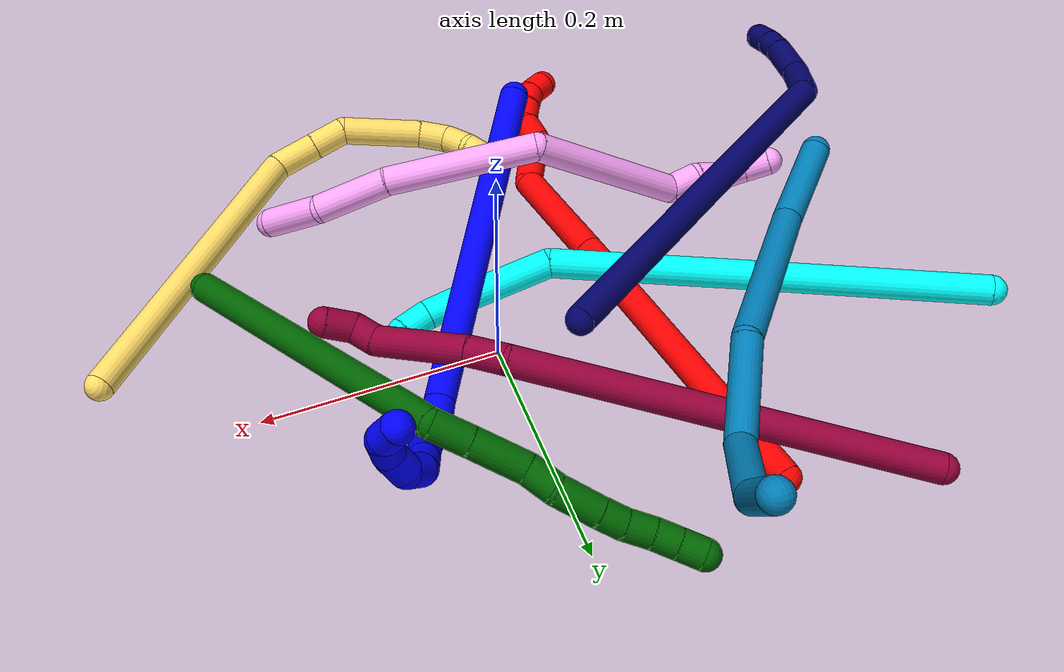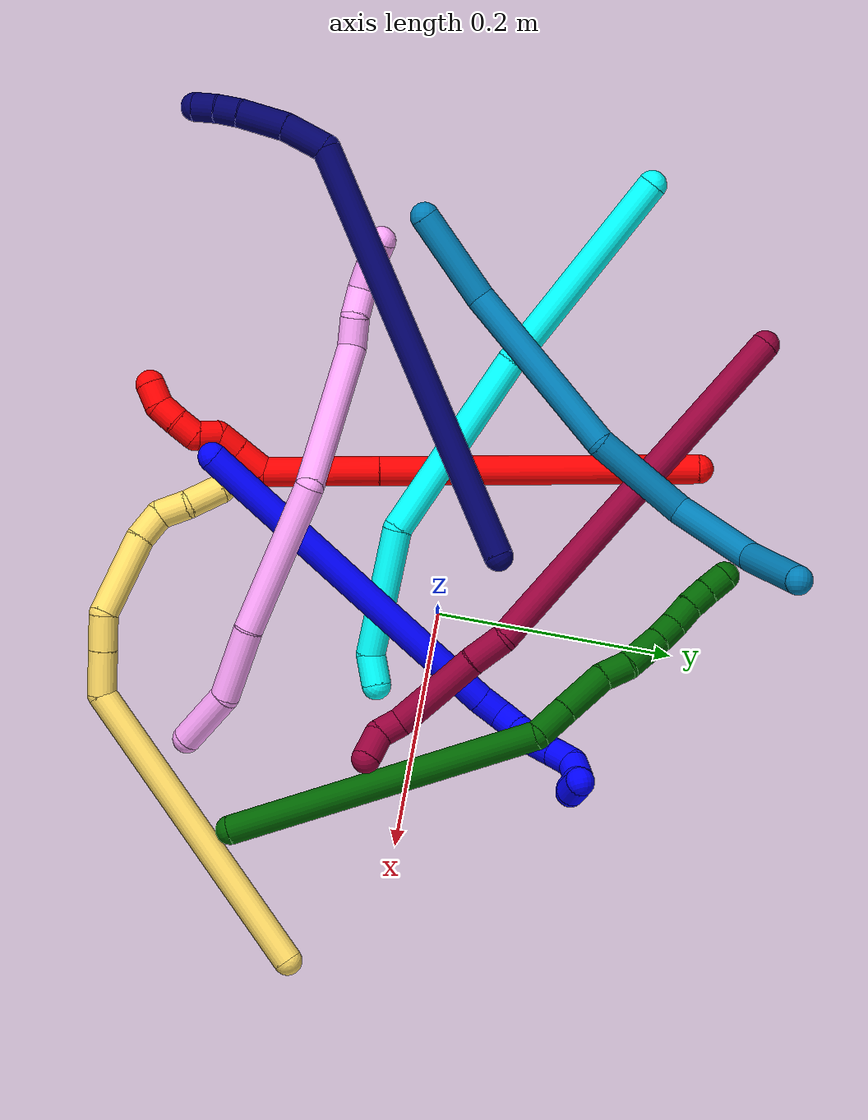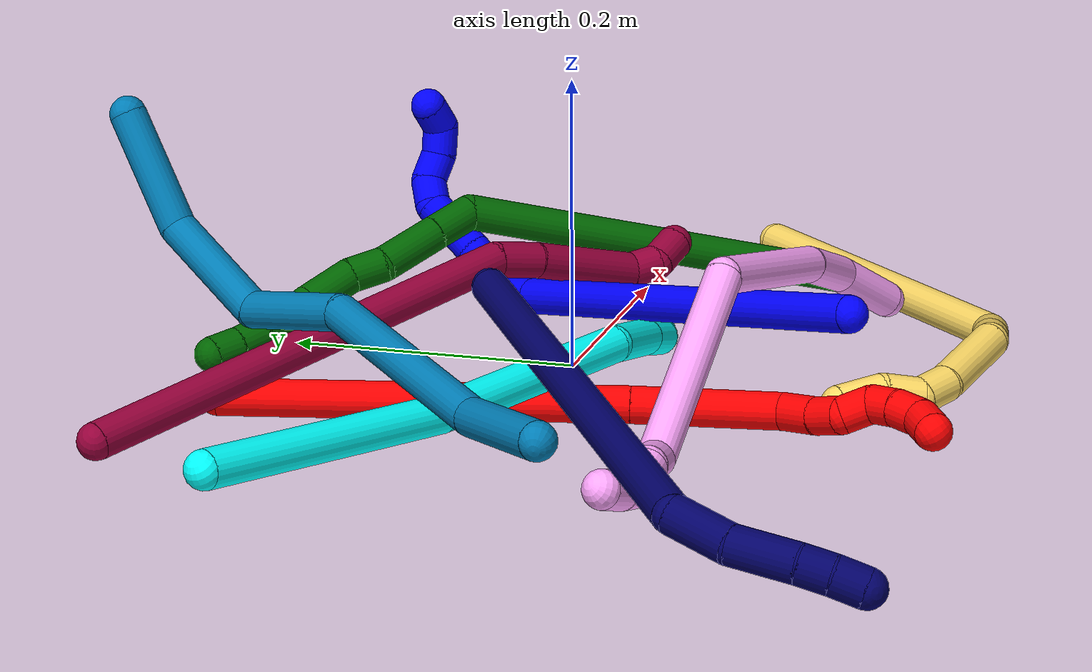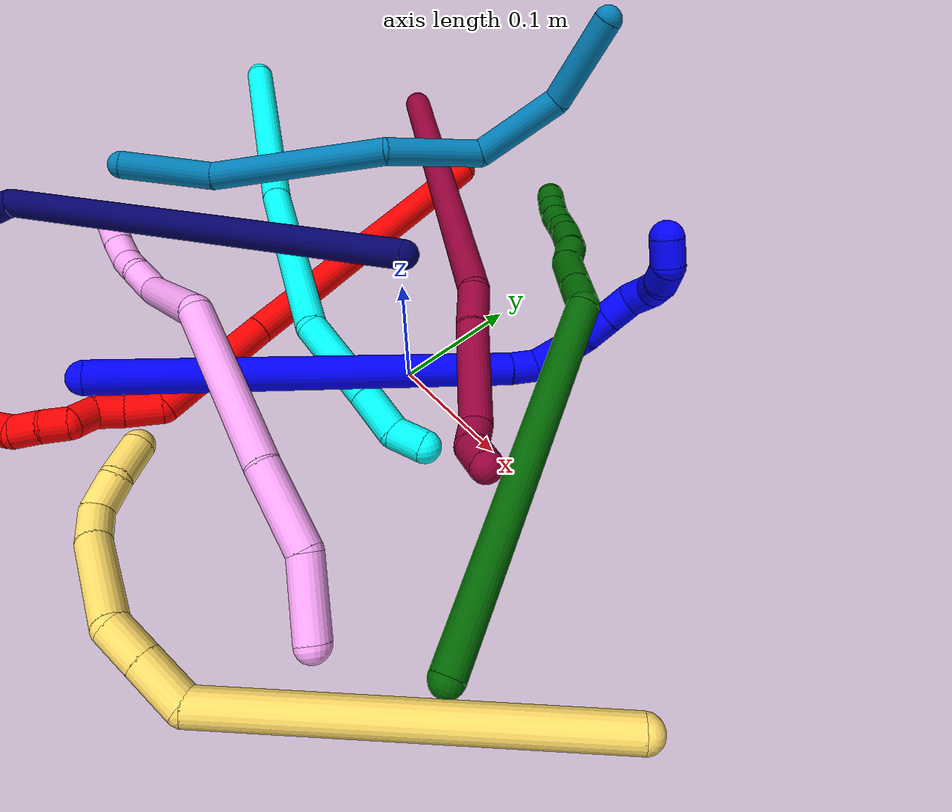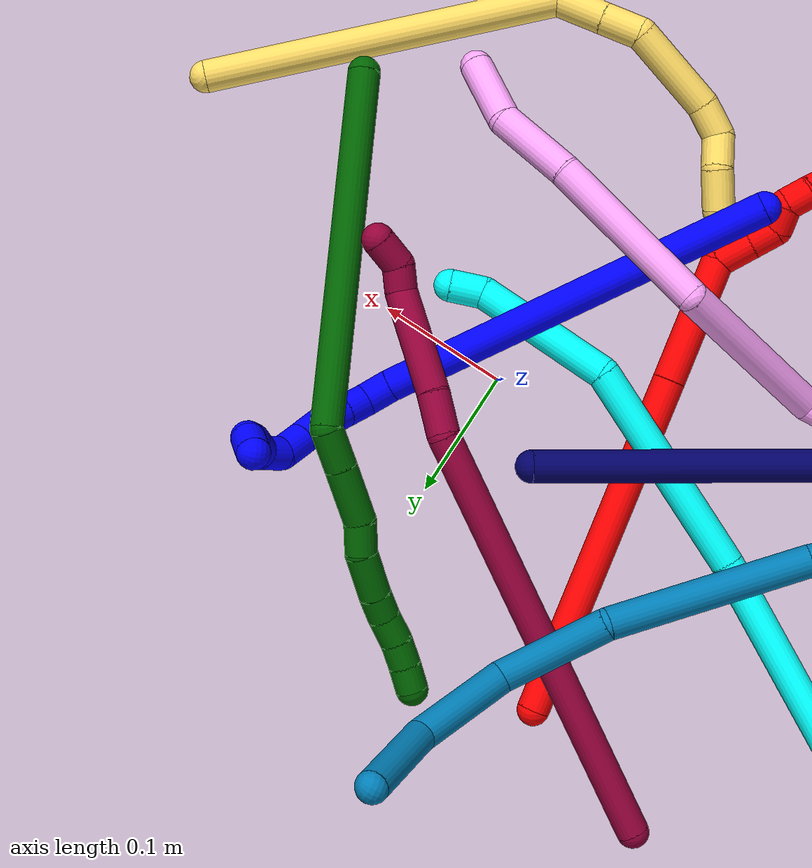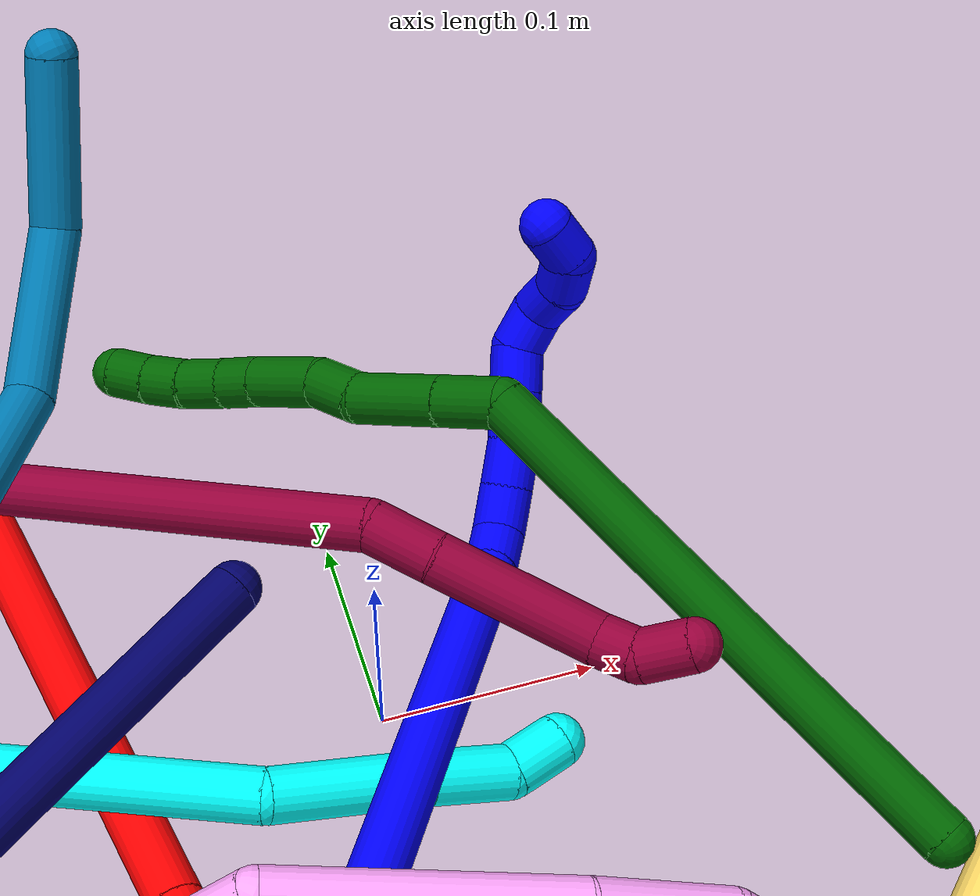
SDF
<sdf version="1.7">
 <world name="default">
  <plugin name="TubeGeneratorPlugin" filename="libtube_generator_plugin.so"/>
  <model name="photoneo_s_sensor">
   <static>1</static>
   <pose>0 0 2 1.57079 1.57079 3.14159</pose>
   <link name="link">
    <inertial><mass>0.1</mass></inertial>
    <sensor name="sensor" type="depth">
     <update_rate>30</update_rate>
     <camera>
      <horizontal_fov>1.22</horizontal_fov>
      <image><width>1920</width><height>1200</height><format>B8G8R8</format></image>
      <clip><near>0.1</near><far>4</far></clip>
      <depth_camera><output>points</output></depth_camera>
     </camera>
     <plugin name="camera_plugin" filename="libgazebo_ros_depth_camera.so">
      <baseline>0.2</baseline>
      <alwaysOn>1</alwaysOn>
      <updateRate>0.0</updateRate>
      <cameraName>camera_ir</cameraName>
      <imageTopicName>/camera/color/image_raw</imageTopicName>
      <cameraInfoTopicName>/camera/color/camera_info</cameraInfoTopicName>
      <depthImageTopicName>/camera/depth/image_raw</depthImageTopicName>
      <depthImageCameraInfoTopicName>/camera/depth/camera_info</depthImageCameraInfoTopicName>
      <pointCloudTopicName>/camera/depth/points</pointCloudTopicName>
      <frameName>fr_optical</frameName>
      <pointCloudCutoff>0.1</pointCloudCutoff>
      <pointCloudCutoffMax>2.0</pointCloudCutoffMax>
      <distortionK1>0</distortionK1>
      <distortionK2>0</distortionK2>
      <distortionK3>0</distortionK3>
      <distortionT1>0</distortionT1>
      <distortionT2>0</distortionT2>
      <CxPrime>0</CxPrime>
      <Cx>0</Cx>
      <Cy>0</Cy>
      <focalLength>0</focalLength>
      <hackBaseline>0</hackBaseline>
     </plugin>
    </sensor>
   </link>
  </model>
  <gravity>0 0 -9.8</gravity>
  <magnetic_field>6e-06 2.3e-05 -4.2e-05</magnetic_field>
  <atmosphere type="adiabatic"/>
  <physics name="default_physics" default="0" type="ode">
   <max_step_size>0.003</max_step_size>
   <real_time_factor>1</real_time_factor>
   <real_time_update_rate>1000</real_time_update_rate>
   <max_contacts>10000</max_contacts>
   <ode>
    <solver>
     <type>quick</type>
     <iters>100</iters>
     <sor>1.3</sor>
     <use_dynamic_moi_rescaling>0</use_dynamic_moi_rescaling>
    </solver>
    <constraints>
     <contact_max_correcting_vel>0</contact_max_correcting_vel>
     <contact_surface_layer>0.001</contact_surface_layer>
     <cfm>0</cfm>
     <erp>0.2</erp>
    </constraints>
   </ode>
  </physics>
  <scene><ambient>0.4 0.4 0.4 1</ambient><background>0.7 0.7 0.7 1</background><shadows>0</shadows></scene>
  <audio><device>default</device></audio>
  <spherical_coordinates>
   <surface_model>EARTH_WGS84</surface_model>
   <latitude_deg>0</latitude_deg>
   <longitude_deg>0</longitude_deg>
   <elevation>0</elevation>
   <heading_deg>0</heading_deg>
  </spherical_coordinates>
  <model name="bin">
   <static>1</static>
   <link name="bottom">
    <collision name="collision-bottom">
     <pose>0 0 -0.01 0 -0 0</pose>
     <geometry><box><size>0.8 0.6 0.02</size></box></geometry>
     <surface>
      <friction><ode><mu>100</mu><mu2>100</mu2></ode></friction>
      <contact><collide_bitmask>65535</collide_bitmask></contact>
     </surface>
    </collision>
   </link>
   <link name="west_wall">
    <collision name="collision-west_wall">
     <pose>-0.41 0 0.1 0 -0 0</pose>
     <geometry><box><size>0.02 0.6 0.2</size></box></geometry>
     <surface>
      <friction><ode><mu>100</mu><mu2>100</mu2></ode></friction>
      <contact><collide_bitmask>65535</collide_bitmask></contact>
     </surface>
    </collision>
   </link>
   <link name="east_wall">
    <collision name="collision-east_wall">
     <pose>0.41 0 0.1 0 -0 0</pose>
     <geometry><box><size>0.02 0.6 0.2</size></box></geometry>
     <surface>
      <friction><ode><mu>100</mu><mu2>100</mu2></ode></friction>
      <contact><collide_bitmask>65535</collide_bitmask></contact>
     </surface>
    </collision>
   </link>
   <link name="south_wall">
    <collision name="collision-south_wall">
     <pose>0 -0.31 0.1 0 -0 0</pose>
     <geometry><box><size>0.8 0.02 0.2</size></box></geometry>
     <surface>
      <friction><ode><mu>100</mu><mu2>100</mu2></ode></friction>
      <contact><collide_bitmask>65535</collide_bitmask></contact>
     </surface>
    </collision>
   </link>
   <link name="north_wall">
    <collision name="collision-north_wall">
     <pose>0 0.31 0.1 0 -0 0</pose>
     <geometry><box><size>0.8 0.02 0.2</size></box></geometry>
     <surface>
      <friction><ode><mu>100</mu><mu2>100</mu2></ode></friction>
      <contact><collide_bitmask>65535</collide_bitmask></contact>
     </surface>
    </collision>
   </link>
  </model>
  <model name="1">
   <static>0</static>
   <link name="1">
    <collision name="collision-cylinder-e_1_1_4">
     <pose>0.001714 0.098719 -0.117489 -2.44279 0.011168 -0.030651</pose>
     <geometry><cylinder><radius>0.0125</radius><length>0.306934</length></cylinder></geometry>
     <surface>
      <friction><ode><mu>1.16</mu><mu2>1.16</mu2><slip1>0</slip1><slip2>0</slip2></ode></friction>
      <contact><ode><kp>1e+06</kp><kd>1</kd><max_vel>0</max_vel><min_depth>0.001</min_depth></ode></contact>
     </surface>
    </collision>
    <visual name="visual-cylinder-e_1_1_4">
     <pose>0.001714 0.098719 -0.117489 -2.44279 0.011168 -0.030651</pose>
     <geometry><cylinder><radius>0.0125</radius><length>0.306934</length></cylinder></geometry>
     <material><ambient>0 0 1 1</ambient></material>
    </visual>
    <collision name="collision-cylinder-e_2_4_5">
     <pose>0.004576 0.20492 -0.243187 -2.40247 0.102972 -0.264515</pose>
     <geometry><cylinder><radius>0.0125</radius><length>0.02233</length></cylinder></geometry>
     <surface>
      <friction><ode><mu>1.16</mu><mu2>1.16</mu2><slip1>0</slip1><slip2>0</slip2></ode></friction>
      <contact><ode><kp>1e+06</kp><kd>1</kd><max_vel>0</max_vel><min_depth>0.001</min_depth></ode></contact>
     </surface>
    </collision>
    <visual name="visual-cylinder-e_2_4_5">
     <pose>0.004576 0.20492 -0.243187 -2.40247 0.102972 -0.264515</pose>
     <geometry><cylinder><radius>0.0125</radius><length>0.02233</length></cylinder></geometry>
     <material><ambient>0 0 1 1</ambient></material>
    </visual>
    <collision name="collision-cylinder-e_3_5_6">
     <pose>0.012551 0.214915 -0.260045 -2.85877 0.648582 -2.34041</pose>
     <geometry><cylinder><radius>0.0125</radius><length>0.022607</length></cylinder></geometry>
     <surface>
      <friction><ode><mu>1.16</mu><mu2>1.16</mu2><slip1>0</slip1><slip2>0</slip2></ode></friction>
      <contact><ode><kp>1e+06</kp><kd>1</kd><max_vel>0</max_vel><min_depth>0.001</min_depth></ode></contact>
     </surface>
    </collision>
    <visual name="visual-cylinder-e_3_5_6">
     <pose>0.012551 0.214915 -0.260045 -2.85877 0.648582 -2.34041</pose>
     <geometry><cylinder><radius>0.0125</radius><length>0.022607</length></cylinder></geometry>
     <material><ambient>0 0 1 1</ambient></material>
    </visual>
    <collision name="collision-cylinder-e_4_6_7">
     <pose>0.026628 0.219336 -0.277107 -2.9187 0.698923 -2.54569</pose>
     <geometry><cylinder><radius>0.0125</radius><length>0.022534</length></cylinder></geometry>
     <surface>
      <friction><ode><mu>1.16</mu><mu2>1.16</mu2><slip1>0</slip1><slip2>0</slip2></ode></friction>
      <contact><ode><kp>1e+06</kp><kd>1</kd><max_vel>0</max_vel><min_depth>0.001</min_depth></ode></contact>
     </surface>
    </collision>
    <visual name="visual-cylinder-e_4_6_7">
     <pose>0.026628 0.219336 -0.277107 -2.9187 0.698923 -2.54569</pose>
     <geometry><cylinder><radius>0.0125</radius><length>0.022534</length></cylinder></geometry>
     <material><ambient>0 0 1 1</ambient></material>
    </visual>
    <collision name="collision-cylinder-e_5_7_8">
     <pose>0.041844 0.224049 -0.292866 -2.77662 0.791823 -2.31007</pose>
     <geometry><cylinder><radius>0.0125</radius><length>0.022388</length></cylinder></geometry>
     <surface>
      <friction><ode><mu>1.16</mu><mu2>1.16</mu2><slip1>0</slip1><slip2>0</slip2></ode></friction>
      <contact><ode><kp>1e+06</kp><kd>1</kd><max_vel>0</max_vel><min_depth>0.001</min_depth></ode></contact>
     </surface>
    </collision>
    <visual name="visual-cylinder-e_5_7_8">
     <pose>0.041844 0.224049 -0.292866 -2.77662 0.791823 -2.31007</pose>
     <geometry><cylinder><radius>0.0125</radius><length>0.022388</length></cylinder></geometry>
     <material><ambient>0 0 1 1</ambient></material>
    </visual>
    <collision name="collision-cylinder-e_6_8_9">
     <pose>0.057536 0.229434 -0.307402 -2.7974 0.791119 -2.35271</pose>
     <geometry><cylinder><radius>0.0125</radius><length>0.021727</length></cylinder></geometry>
     <surface>
      <friction><ode><mu>1.16</mu><mu2>1.16</mu2><slip1>0</slip1><slip2>0</slip2></ode></friction>
      <contact><ode><kp>1e+06</kp><kd>1</kd><max_vel>0</max_vel><min_depth>0.001</min_depth></ode></contact>
     </surface>
    </collision>
    <visual name="visual-cylinder-e_6_8_9">
     <pose>0.057536 0.229434 -0.307402 -2.7974 0.791119 -2.35271</pose>
     <geometry><cylinder><radius>0.0125</radius><length>0.021727</length></cylinder></geometry>
     <material><ambient>0 0 1 1</ambient></material>
    </visual>
    <collision name="collision-cylinder-e_7_9_10">
     <pose>0.070588 0.229561 -0.323027 2.85889 0.545209 2.19993</pose>
     <geometry><cylinder><radius>0.0125</radius><length>0.020545</length></cylinder></geometry>
     <surface>
      <friction><ode><mu>1.16</mu><mu2>1.16</mu2><slip1>0</slip1><slip2>0</slip2></ode></friction>
      <contact><ode><kp>1e+06</kp><kd>1</kd><max_vel>0</max_vel><min_depth>0.001</min_depth></ode></contact>
     </surface>
    </collision>
    <visual name="visual-cylinder-e_7_9_10">
     <pose>0.070588 0.229561 -0.323027 2.85889 0.545209 2.19993</pose>
     <geometry><cylinder><radius>0.0125</radius><length>0.020545</length></cylinder></geometry>
     <material><ambient>0 0 1 1</ambient></material>
    </visual>
    <collision name="collision-cylinder-e_8_10_11">
     <pose>0.080709 0.219191 -0.336322 2.12129 0.476174 0.818467</pose>
     <geometry><cylinder><radius>0.0125</radius><length>0.020911</length></cylinder></geometry>
     <surface>
      <friction><ode><mu>1.16</mu><mu2>1.16</mu2><slip1>0</slip1><slip2>0</slip2></ode></friction>
      <contact><ode><kp>1e+06</kp><kd>1</kd><max_vel>0</max_vel><min_depth>0.001</min_depth></ode></contact>
     </surface>
    </collision>
    <visual name="visual-cylinder-e_8_10_11">
     <pose>0.080709 0.219191 -0.336322 2.12129 0.476174 0.818467</pose>
     <geometry><cylinder><radius>0.0125</radius><length>0.020911</length></cylinder></geometry>
     <material><ambient>0 0 1 1</ambient></material>
    </visual>
    <collision name="collision-cylinder-e_9_11_12">
     <pose>0.093041 0.205614 -0.344537 2.10589 0.853601 1.34731</pose>
     <geometry><cylinder><radius>0.0125</radius><length>0.02001</length></cylinder></geometry>
     <surface>
      <friction><ode><mu>1.16</mu><mu2>1.16</mu2><slip1>0</slip1><slip2>0</slip2></ode></friction>
      <contact><ode><kp>1e+06</kp><kd>1</kd><max_vel>0</max_vel><min_depth>0.001</min_depth></ode></contact>
     </surface>
    </collision>
    <visual name="visual-cylinder-e_9_11_12">
     <pose>0.093041 0.205614 -0.344537 2.10589 0.853601 1.34731</pose>
     <geometry><cylinder><radius>0.0125</radius><length>0.02001</length></cylinder></geometry>
     <material><ambient>0 0 1 1</ambient></material>
    </visual>
    <collision name="collision-cylinder-e_10_12_2">
     <pose>0.110455 0.199297 -0.346409 0.419883 1.40803 0.358014</pose>
     <geometry><cylinder><radius>0.0125</radius><length>0.020012</length></cylinder></geometry>
     <surface>
      <friction><ode><mu>1.16</mu><mu2>1.16</mu2><slip1>0</slip1><slip2>0</slip2></ode></friction>
      <contact><ode><kp>1e+06</kp><kd>1</kd><max_vel>0</max_vel><min_depth>0.001</min_depth></ode></contact>
     </surface>
    </collision>
    <visual name="visual-cylinder-e_10_12_2">
     <pose>0.110455 0.199297 -0.346409 0.419883 1.40803 0.358014</pose>
     <geometry><cylinder><radius>0.0125</radius><length>0.020012</length></cylinder></geometry>
     <material><ambient>0 0 1 1</ambient></material>
    </visual>
    <collision name="collision-sphere-2">
     <pose>0.120329 0.198636 -0.344929 0 -0 0</pose>
     <geometry><sphere><radius>0.0125</radius></sphere></geometry>
     <surface>
      <friction><ode><mu>1.16</mu><mu2>1.16</mu2><slip1>0</slip1><slip2>0</slip2></ode></friction>
      <contact><ode><kp>1e+06</kp><kd>1</kd><max_vel>0</max_vel><min_depth>0.001</min_depth></ode></contact>
     </surface>
    </collision>
    <visual name="visual-sphere-2">
     <pose>0.120329 0.198636 -0.344929 0 -0 0</pose>
     <geometry><sphere><radius>0.0125</radius></sphere></geometry>
     <material><ambient>0 0 1 1</ambient></material>
    </visual>
    <collision name="collision-sphere-12">
     <pose>0.100582 0.199958 -0.34789 0 -0 0</pose>
     <geometry><sphere><radius>0.0125</radius></sphere></geometry>
     <surface>
      <friction><ode><mu>1.16</mu><mu2>1.16</mu2><slip1>0</slip1><slip2>0</slip2></ode></friction>
      <contact><ode><kp>1e+06</kp><kd>1</kd><max_vel>0</max_vel><min_depth>0.001</min_depth></ode></contact>
     </surface>
    </collision>
    <visual name="visual-sphere-12">
     <pose>0.100582 0.199958 -0.34789 0 -0 0</pose>
     <geometry><sphere><radius>0.0125</radius></sphere></geometry>
     <material><ambient>0 0 1 1</ambient></material>
    </visual>
    <collision name="collision-sphere-11">
     <pose>0.085501 0.211271 -0.341183 0 -0 0</pose>
     <geometry><sphere><radius>0.0125</radius></sphere></geometry>
     <surface>
      <friction><ode><mu>1.16</mu><mu2>1.16</mu2><slip1>0</slip1><slip2>0</slip2></ode></friction>
      <contact><ode><kp>1e+06</kp><kd>1</kd><max_vel>0</max_vel><min_depth>0.001</min_depth></ode></contact>
     </surface>
    </collision>
    <visual name="visual-sphere-11">
     <pose>0.085501 0.211271 -0.341183 0 -0 0</pose>
     <geometry><sphere><radius>0.0125</radius></sphere></geometry>
     <material><ambient>0 0 1 1</ambient></material>
    </visual>
    <collision name="collision-sphere-10">
     <pose>0.075916 0.22711 -0.331461 0 -0 0</pose>
     <geometry><sphere><radius>0.0125</radius></sphere></geometry>
     <surface>
      <friction><ode><mu>1.16</mu><mu2>1.16</mu2><slip1>0</slip1><slip2>0</slip2></ode></friction>
      <contact><ode><kp>1e+06</kp><kd>1</kd><max_vel>0</max_vel><min_depth>0.001</min_depth></ode></contact>
     </surface>
    </collision>
    <visual name="visual-sphere-10">
     <pose>0.075916 0.22711 -0.331461 0 -0 0</pose>
     <geometry><sphere><radius>0.0125</radius></sphere></geometry>
     <material><ambient>0 0 1 1</ambient></material>
    </visual>
    <collision name="collision-sphere-9">
     <pose>0.065261 0.232011 -0.314592 0 -0 0</pose>
     <geometry><sphere><radius>0.0125</radius></sphere></geometry>
     <surface>
      <friction><ode><mu>1.16</mu><mu2>1.16</mu2><slip1>0</slip1><slip2>0</slip2></ode></friction>
      <contact><ode><kp>1e+06</kp><kd>1</kd><max_vel>0</max_vel><min_depth>0.001</min_depth></ode></contact>
     </surface>
    </collision>
    <visual name="visual-sphere-9">
     <pose>0.065261 0.232011 -0.314592 0 -0 0</pose>
     <geometry><sphere><radius>0.0125</radius></sphere></geometry>
     <material><ambient>0 0 1 1</ambient></material>
    </visual>
    <collision name="collision-sphere-4">
     <pose>0.003428 0.197438 -0.234979 0 -0 0</pose>
     <geometry><sphere><radius>0.0125</radius></sphere></geometry>
     <surface>
      <friction><ode><mu>1.16</mu><mu2>1.16</mu2><slip1>0</slip1><slip2>0</slip2></ode></friction>
      <contact><ode><kp>1e+06</kp><kd>1</kd><max_vel>0</max_vel><min_depth>0.001</min_depth></ode></contact>
     </surface>
    </collision>
    <visual name="visual-sphere-4">
     <pose>0.003428 0.197438 -0.234979 0 -0 0</pose>
     <geometry><sphere><radius>0.0125</radius></sphere></geometry>
     <material><ambient>0 0 1 1</ambient></material>
    </visual>
    <collision name="collision-sphere-1">
     <geometry><sphere><radius>0.0125</radius></sphere></geometry>
     <surface>
      <friction><ode><mu>1.16</mu><mu2>1.16</mu2><slip1>0</slip1><slip2>0</slip2></ode></friction>
      <contact><ode><kp>1e+06</kp><kd>1</kd><max_vel>0</max_vel><min_depth>0.001</min_depth></ode></contact>
     </surface>
    </collision>
    <visual name="visual-sphere-1">
     <geometry><sphere><radius>0.0125</radius></sphere></geometry>
     <material><ambient>0 0 1 1</ambient></material>
    </visual>
    <collision name="collision-sphere-8">
     <pose>0.04981 0.226856 -0.300212 0 -0 0</pose>
     <geometry><sphere><radius>0.0125</radius></sphere></geometry>
     <surface>
      <friction><ode><mu>1.16</mu><mu2>1.16</mu2><slip1>0</slip1><slip2>0</slip2></ode></friction>
      <contact><ode><kp>1e+06</kp><kd>1</kd><max_vel>0</max_vel><min_depth>0.001</min_depth></ode></contact>
     </surface>
    </collision>
    <visual name="visual-sphere-8">
     <pose>0.04981 0.226856 -0.300212 0 -0 0</pose>
     <geometry><sphere><radius>0.0125</radius></sphere></geometry>
     <material><ambient>0 0 1 1</ambient></material>
    </visual>
    <collision name="collision-sphere-5">
     <pose>0.005723 0.212401 -0.251395 0 -0 0</pose>
     <geometry><sphere><radius>0.0125</radius></sphere></geometry>
     <surface>
      <friction><ode><mu>1.16</mu><mu2>1.16</mu2><slip1>0</slip1><slip2>0</slip2></ode></friction>
      <contact><ode><kp>1e+06</kp><kd>1</kd><max_vel>0</max_vel><min_depth>0.001</min_depth></ode></contact>
     </surface>
    </collision>
    <visual name="visual-sphere-5">
     <pose>0.005723 0.212401 -0.251395 0 -0 0</pose>
     <geometry><sphere><radius>0.0125</radius></sphere></geometry>
     <material><ambient>0 0 1 1</ambient></material>
    </visual>
    <collision name="collision-sphere-6">
     <pose>0.019379 0.217429 -0.268695 0 -0 0</pose>
     <geometry><sphere><radius>0.0125</radius></sphere></geometry>
     <surface>
      <friction><ode><mu>1.16</mu><mu2>1.16</mu2><slip1>0</slip1><slip2>0</slip2></ode></friction>
      <contact><ode><kp>1e+06</kp><kd>1</kd><max_vel>0</max_vel><min_depth>0.001</min_depth></ode></contact>
     </surface>
    </collision>
    <visual name="visual-sphere-6">
     <pose>0.019379 0.217429 -0.268695 0 -0 0</pose>
     <geometry><sphere><radius>0.0125</radius></sphere></geometry>
     <material><ambient>0 0 1 1</ambient></material>
    </visual>
    <collision name="collision-sphere-7">
     <pose>0.033878 0.221242 -0.28552 0 -0 0</pose>
     <geometry><sphere><radius>0.0125</radius></sphere></geometry>
     <surface>
      <friction><ode><mu>1.16</mu><mu2>1.16</mu2><slip1>0</slip1><slip2>0</slip2></ode></friction>
      <contact><ode><kp>1e+06</kp><kd>1</kd><max_vel>0</max_vel><min_depth>0.001</min_depth></ode></contact>
     </surface>
    </collision>
    <visual name="visual-sphere-7">
     <pose>0.033878 0.221242 -0.28552 0 -0 0</pose>
     <geometry><sphere><radius>0.0125</radius></sphere></geometry>
     <material><ambient>0 0 1 1</ambient></material>
    </visual>
    <inertial>
     <pose>0.021818 0.144162 -0.188694 0 -0 0</pose>
     <mass>0.5</mass>
     <inertia>
      <ixx>0.002353</ixx>
      <ixy>0</ixy>
      <ixz>0</ixz>
      <iyy>-0.001904</iyy>
      <iyz>0</iyz>
      <izz>-0.001621</izz>
     </inertia>
    </inertial>
   </link>
   <pose>-0.092048 -0.209417 0.080739 -1.93074 -0.990187 2.29936</pose>
  </model>
  <model name="2">
   <static>0</static>
   <link name="2">
    <collision name="collision-cylinder-e_1_1_4">
     <pose>0.014676 -0.077544 0.110071 0.613736 0.108572 0.034434</pose>
     <geometry><cylinder><radius>0.0125</radius><length>0.27088</length></cylinder></geometry>
     <surface>
      <friction><ode><mu>1.16</mu><mu2>1.16</mu2><slip1>0</slip1><slip2>0</slip2></ode></friction>
      <contact><ode><kp>1e+06</kp><kd>1</kd><max_vel>0</max_vel><min_depth>0.001</min_depth></ode></contact>
     </surface>
    </collision>
    <visual name="visual-cylinder-e_1_1_4">
     <pose>0.014676 -0.077544 0.110071 0.613736 0.108572 0.034434</pose>
     <geometry><cylinder><radius>0.0125</radius><length>0.27088</length></cylinder></geometry>
     <material><ambient>1 0 0 1</ambient></material>
    </visual>
    <collision name="collision-cylinder-e_2_4_5">
     <pose>0.035515 -0.184013 0.259519 0.633533 0.125463 0.041176</pose>
     <geometry><cylinder><radius>0.0125</radius><length>0.098493</length></cylinder></geometry>
     <surface>
      <friction><ode><mu>1.16</mu><mu2>1.16</mu2><slip1>0</slip1><slip2>0</slip2></ode></friction>
      <contact><ode><kp>1e+06</kp><kd>1</kd><max_vel>0</max_vel><min_depth>0.001</min_depth></ode></contact>
     </surface>
    </collision>
    <visual name="visual-cylinder-e_2_4_5">
     <pose>0.035515 -0.184013 0.259519 0.633533 0.125463 0.041176</pose>
     <geometry><cylinder><radius>0.0125</radius><length>0.098493</length></cylinder></geometry>
     <material><ambient>1 0 0 1</ambient></material>
    </visual>
    <collision name="collision-cylinder-e_3_5_6">
     <pose>0.035015 -0.223333 0.305974 0.973129 -0.487144 -0.261412</pose>
     <geometry><cylinder><radius>0.0125</radius><length>0.028463</length></cylinder></geometry>
     <surface>
      <friction><ode><mu>1.16</mu><mu2>1.16</mu2><slip1>0</slip1><slip2>0</slip2></ode></friction>
      <contact><ode><kp>1e+06</kp><kd>1</kd><max_vel>0</max_vel><min_depth>0.001</min_depth></ode></contact>
     </surface>
    </collision>
    <visual name="visual-cylinder-e_3_5_6">
     <pose>0.035015 -0.223333 0.305974 0.973129 -0.487144 -0.261412</pose>
     <geometry><cylinder><radius>0.0125</radius><length>0.028463</length></cylinder></geometry>
     <material><ambient>1 0 0 1</ambient></material>
    </visual>
    <collision name="collision-cylinder-e_4_6_7">
     <pose>0.022578 -0.240584 0.319042 0.852449 -0.565281 -0.262218</pose>
     <geometry><cylinder><radius>0.0125</radius><length>0.021563</length></cylinder></geometry>
     <surface>
      <friction><ode><mu>1.16</mu><mu2>1.16</mu2><slip1>0</slip1><slip2>0</slip2></ode></friction>
      <contact><ode><kp>1e+06</kp><kd>1</kd><max_vel>0</max_vel><min_depth>0.001</min_depth></ode></contact>
     </surface>
    </collision>
    <visual name="visual-cylinder-e_4_6_7">
     <pose>0.022578 -0.240584 0.319042 0.852449 -0.565281 -0.262218</pose>
     <geometry><cylinder><radius>0.0125</radius><length>0.021563</length></cylinder></geometry>
     <material><ambient>1 0 0 1</ambient></material>
    </visual>
    <collision name="collision-cylinder-e_5_7_8">
     <pose>0.01592 -0.250308 0.334869 0.283909 -0.085961 -0.012293</pose>
     <geometry><cylinder><radius>0.0125</radius><length>0.020565</length></cylinder></geometry>
     <surface>
      <friction><ode><mu>1.16</mu><mu2>1.16</mu2><slip1>0</slip1><slip2>0</slip2></ode></friction>
      <contact><ode><kp>1e+06</kp><kd>1</kd><max_vel>0</max_vel><min_depth>0.001</min_depth></ode></contact>
     </surface>
    </collision>
    <visual name="visual-cylinder-e_5_7_8">
     <pose>0.01592 -0.250308 0.334869 0.283909 -0.085961 -0.012293</pose>
     <geometry><cylinder><radius>0.0125</radius><length>0.020565</length></cylinder></geometry>
     <material><ambient>1 0 0 1</ambient></material>
    </visual>
    <collision name="collision-cylinder-e_6_8_9">
     <pose>0.010561 -0.260717 0.349544 0.999997 -0.463332 -0.256333</pose>
     <geometry><cylinder><radius>0.0125</radius><length>0.020031</length></cylinder></geometry>
     <surface>
      <friction><ode><mu>1.16</mu><mu2>1.16</mu2><slip1>0</slip1><slip2>0</slip2></ode></friction>
      <contact><ode><kp>1e+06</kp><kd>1</kd><max_vel>0</max_vel><min_depth>0.001</min_depth></ode></contact>
     </surface>
    </collision>
    <visual name="visual-cylinder-e_6_8_9">
     <pose>0.010561 -0.260717 0.349544 0.999997 -0.463332 -0.256333</pose>
     <geometry><cylinder><radius>0.0125</radius><length>0.020031</length></cylinder></geometry>
     <material><ambient>1 0 0 1</ambient></material>
    </visual>
    <collision name="collision-cylinder-e_7_9_10">
     <pose>0.002273 -0.276765 0.358003 1.16879 -0.391078 -0.26055</pose>
     <geometry><cylinder><radius>0.0125</radius><length>0.020002</length></cylinder></geometry>
     <surface>
      <friction><ode><mu>1.16</mu><mu2>1.16</mu2><slip1>0</slip1><slip2>0</slip2></ode></friction>
      <contact><ode><kp>1e+06</kp><kd>1</kd><max_vel>0</max_vel><min_depth>0.001</min_depth></ode></contact>
     </surface>
    </collision>
    <visual name="visual-cylinder-e_7_9_10">
     <pose>0.002273 -0.276765 0.358003 1.16879 -0.391078 -0.26055</pose>
     <geometry><cylinder><radius>0.0125</radius><length>0.020002</length></cylinder></geometry>
     <material><ambient>1 0 0 1</ambient></material>
    </visual>
    <collision name="collision-cylinder-e_8_10_2">
     <pose>-0.007347 -0.293409 0.361287 1.61172 -0.619603 -0.64377</pose>
     <geometry><cylinder><radius>0.0125</radius><length>0.020002</length></cylinder></geometry>
     <surface>
      <friction><ode><mu>1.16</mu><mu2>1.16</mu2><slip1>0</slip1><slip2>0</slip2></ode></friction>
      <contact><ode><kp>1e+06</kp><kd>1</kd><max_vel>0</max_vel><min_depth>0.001</min_depth></ode></contact>
     </surface>
    </collision>
    <visual name="visual-cylinder-e_8_10_2">
     <pose>-0.007347 -0.293409 0.361287 1.61172 -0.619603 -0.64377</pose>
     <geometry><cylinder><radius>0.0125</radius><length>0.020002</length></cylinder></geometry>
     <material><ambient>1 0 0 1</ambient></material>
    </visual>
    <collision name="collision-sphere-2">
     <pose>-0.013155 -0.301544 0.360954 0 -0 0</pose>
     <geometry><sphere><radius>0.0125</radius></sphere></geometry>
     <surface>
      <friction><ode><mu>1.16</mu><mu2>1.16</mu2><slip1>0</slip1><slip2>0</slip2></ode></friction>
      <contact><ode><kp>1e+06</kp><kd>1</kd><max_vel>0</max_vel><min_depth>0.001</min_depth></ode></contact>
     </surface>
    </collision>
    <visual name="visual-sphere-2">
     <pose>-0.013155 -0.301544 0.360954 0 -0 0</pose>
     <geometry><sphere><radius>0.0125</radius></sphere></geometry>
     <material><ambient>1 0 0 1</ambient></material>
    </visual>
    <collision name="collision-sphere-10">
     <pose>-0.00154 -0.285274 0.36162 0 -0 0</pose>
     <geometry><sphere><radius>0.0125</radius></sphere></geometry>
     <surface>
      <friction><ode><mu>1.16</mu><mu2>1.16</mu2><slip1>0</slip1><slip2>0</slip2></ode></friction>
      <contact><ode><kp>1e+06</kp><kd>1</kd><max_vel>0</max_vel><min_depth>0.001</min_depth></ode></contact>
     </surface>
    </collision>
    <visual name="visual-sphere-10">
     <pose>-0.00154 -0.285274 0.36162 0 -0 0</pose>
     <geometry><sphere><radius>0.0125</radius></sphere></geometry>
     <material><ambient>1 0 0 1</ambient></material>
    </visual>
    <collision name="collision-sphere-9">
     <pose>0.006085 -0.268256 0.354385 0 -0 0</pose>
     <geometry><sphere><radius>0.0125</radius></sphere></geometry>
     <surface>
      <friction><ode><mu>1.16</mu><mu2>1.16</mu2><slip1>0</slip1><slip2>0</slip2></ode></friction>
      <contact><ode><kp>1e+06</kp><kd>1</kd><max_vel>0</max_vel><min_depth>0.001</min_depth></ode></contact>
     </surface>
    </collision>
    <visual name="visual-sphere-9">
     <pose>0.006085 -0.268256 0.354385 0 -0 0</pose>
     <geometry><sphere><radius>0.0125</radius></sphere></geometry>
     <material><ambient>1 0 0 1</ambient></material>
    </visual>
    <collision name="collision-sphere-4">
     <pose>0.029352 -0.155088 0.220141 0 -0 0</pose>
     <geometry><sphere><radius>0.0125</radius></sphere></geometry>
     <surface>
      <friction><ode><mu>1.16</mu><mu2>1.16</mu2><slip1>0</slip1><slip2>0</slip2></ode></friction>
      <contact><ode><kp>1e+06</kp><kd>1</kd><max_vel>0</max_vel><min_depth>0.001</min_depth></ode></contact>
     </surface>
    </collision>
    <visual name="visual-sphere-4">
     <pose>0.029352 -0.155088 0.220141 0 -0 0</pose>
     <geometry><sphere><radius>0.0125</radius></sphere></geometry>
     <material><ambient>1 0 0 1</ambient></material>
    </visual>
    <collision name="collision-sphere-1">
     <geometry><sphere><radius>0.0125</radius></sphere></geometry>
     <surface>
      <friction><ode><mu>1.16</mu><mu2>1.16</mu2><slip1>0</slip1><slip2>0</slip2></ode></friction>
      <contact><ode><kp>1e+06</kp><kd>1</kd><max_vel>0</max_vel><min_depth>0.001</min_depth></ode></contact>
     </surface>
    </collision>
    <visual name="visual-sphere-1">
     <geometry><sphere><radius>0.0125</radius></sphere></geometry>
     <material><ambient>1 0 0 1</ambient></material>
    </visual>
    <collision name="collision-sphere-8">
     <pose>0.015037 -0.253178 0.344703 0 -0 0</pose>
     <geometry><sphere><radius>0.0125</radius></sphere></geometry>
     <surface>
      <friction><ode><mu>1.16</mu><mu2>1.16</mu2><slip1>0</slip1><slip2>0</slip2></ode></friction>
      <contact><ode><kp>1e+06</kp><kd>1</kd><max_vel>0</max_vel><min_depth>0.001</min_depth></ode></contact>
     </surface>
    </collision>
    <visual name="visual-sphere-8">
     <pose>0.015037 -0.253178 0.344703 0 -0 0</pose>
     <geometry><sphere><radius>0.0125</radius></sphere></geometry>
     <material><ambient>1 0 0 1</ambient></material>
    </visual>
    <collision name="collision-sphere-5">
     <pose>0.041677 -0.212937 0.298897 0 -0 0</pose>
     <geometry><sphere><radius>0.0125</radius></sphere></geometry>
     <surface>
      <friction><ode><mu>1.16</mu><mu2>1.16</mu2><slip1>0</slip1><slip2>0</slip2></ode></friction>
      <contact><ode><kp>1e+06</kp><kd>1</kd><max_vel>0</max_vel><min_depth>0.001</min_depth></ode></contact>
     </surface>
    </collision>
    <visual name="visual-sphere-5">
     <pose>0.041677 -0.212937 0.298897 0 -0 0</pose>
     <geometry><sphere><radius>0.0125</radius></sphere></geometry>
     <material><ambient>1 0 0 1</ambient></material>
    </visual>
    <collision name="collision-sphere-6">
     <pose>0.028353 -0.23373 0.313051 0 -0 0</pose>
     <geometry><sphere><radius>0.0125</radius></sphere></geometry>
     <surface>
      <friction><ode><mu>1.16</mu><mu2>1.16</mu2><slip1>0</slip1><slip2>0</slip2></ode></friction>
      <contact><ode><kp>1e+06</kp><kd>1</kd><max_vel>0</max_vel><min_depth>0.001</min_depth></ode></contact>
     </surface>
    </collision>
    <visual name="visual-sphere-6">
     <pose>0.028353 -0.23373 0.313051 0 -0 0</pose>
     <geometry><sphere><radius>0.0125</radius></sphere></geometry>
     <material><ambient>1 0 0 1</ambient></material>
    </visual>
    <collision name="collision-sphere-7">
     <pose>0.016803 -0.247439 0.325034 0 -0 0</pose>
     <geometry><sphere><radius>0.0125</radius></sphere></geometry>
     <surface>
      <friction><ode><mu>1.16</mu><mu2>1.16</mu2><slip1>0</slip1><slip2>0</slip2></ode></friction>
      <contact><ode><kp>1e+06</kp><kd>1</kd><max_vel>0</max_vel><min_depth>0.001</min_depth></ode></contact>
     </surface>
    </collision>
    <visual name="visual-sphere-7">
     <pose>0.016803 -0.247439 0.325034 0 -0 0</pose>
     <geometry><sphere><radius>0.0125</radius></sphere></geometry>
     <material><ambient>1 0 0 1</ambient></material>
    </visual>
    <inertial>
     <pose>0.018789 -0.144897 0.198482 0 -0 0</pose>
     <mass>0.5</mass>
     <inertia>
      <ixx>0.001805</ixx>
      <ixy>0</ixy>
      <ixz>0</ixz>
      <iyy>0.001474</iyy>
      <iyz>0</iyz>
      <izz>0.000852</izz>
     </inertia>
    </inertial>
   </link>
   <pose>-0.160072 0.195594 0.011497 0.859408 0.682215 0.042586</pose>
  </model>
  <model name="3">
   <static>0</static>
   <link name="3">
    <collision name="collision-cylinder-e_1_1_4">
     <pose>0.062931 -0.042581 -0.058183 2.50981 0.717602 1.70792</pose>
     <geometry><cylinder><radius>0.0125</radius><length>0.191403</length></cylinder></geometry>
     <surface>
      <friction><ode><mu>1.16</mu><mu2>1.16</mu2><slip1>0</slip1><slip2>0</slip2></ode></friction>
      <contact><ode><kp>1e+06</kp><kd>1</kd><max_vel>0</max_vel><min_depth>0.001</min_depth></ode></contact>
     </surface>
    </collision>
    <visual name="visual-cylinder-e_1_1_4">
     <pose>0.062931 -0.042581 -0.058183 2.50981 0.717602 1.70792</pose>
     <geometry><cylinder><radius>0.0125</radius><length>0.191403</length></cylinder></geometry>
     <material><ambient>0.003922 1 0.996078 1</ambient></material>
    </visual>
    <collision name="collision-cylinder-e_2_4_5">
     <pose>0.189306 -0.11956 -0.162366 2.49952 0.835036 1.85505</pose>
     <geometry><cylinder><radius>0.0125</radius><length>0.171163</length></cylinder></geometry>
     <surface>
      <friction><ode><mu>1.16</mu><mu2>1.16</mu2><slip1>0</slip1><slip2>0</slip2></ode></friction>
      <contact><ode><kp>1e+06</kp><kd>1</kd><max_vel>0</max_vel><min_depth>0.001</min_depth></ode></contact>
     </surface>
    </collision>
    <visual name="visual-cylinder-e_2_4_5">
     <pose>0.189306 -0.11956 -0.162366 2.49952 0.835036 1.85505</pose>
     <geometry><cylinder><radius>0.0125</radius><length>0.171163</length></cylinder></geometry>
     <material><ambient>0.003922 1 0.996078 1</ambient></material>
    </visual>
    <collision name="collision-cylinder-e_3_5_6">
     <pose>0.279513 -0.153011 -0.233069 -3.10332 0.825035 -3.05419</pose>
     <geometry><cylinder><radius>0.0125</radius><length>0.072867</length></cylinder></geometry>
     <surface>
      <friction><ode><mu>1.16</mu><mu2>1.16</mu2><slip1>0</slip1><slip2>0</slip2></ode></friction>
      <contact><ode><kp>1e+06</kp><kd>1</kd><max_vel>0</max_vel><min_depth>0.001</min_depth></ode></contact>
     </surface>
    </collision>
    <visual name="visual-cylinder-e_3_5_6">
     <pose>0.279513 -0.153011 -0.233069 -3.10332 0.825035 -3.05419</pose>
     <geometry><cylinder><radius>0.0125</radius><length>0.072867</length></cylinder></geometry>
     <material><ambient>0.003922 1 0.996078 1</ambient></material>
    </visual>
    <collision name="collision-cylinder-e_4_6_7">
     <pose>0.31945 -0.151327 -0.271327 -3.08716 0.770381 -3.00751</pose>
     <geometry><cylinder><radius>0.0125</radius><length>0.037834</length></cylinder></geometry>
     <surface>
      <friction><ode><mu>1.16</mu><mu2>1.16</mu2><slip1>0</slip1><slip2>0</slip2></ode></friction>
      <contact><ode><kp>1e+06</kp><kd>1</kd><max_vel>0</max_vel><min_depth>0.001</min_depth></ode></contact>
     </surface>
    </collision>
    <visual name="visual-cylinder-e_4_6_7">
     <pose>0.31945 -0.151327 -0.271327 -3.08716 0.770381 -3.00751</pose>
     <geometry><cylinder><radius>0.0125</radius><length>0.037834</length></cylinder></geometry>
     <material><ambient>0.003922 1 0.996078 1</ambient></material>
    </visual>
    <collision name="collision-cylinder-e_5_7_2">
     <pose>0.344021 -0.146096 -0.29023 -2.44283 1.02107 -1.98812</pose>
     <geometry><cylinder><radius>0.0125</radius><length>0.026733</length></cylinder></geometry>
     <surface>
      <friction><ode><mu>1.16</mu><mu2>1.16</mu2><slip1>0</slip1><slip2>0</slip2></ode></friction>
      <contact><ode><kp>1e+06</kp><kd>1</kd><max_vel>0</max_vel><min_depth>0.001</min_depth></ode></contact>
     </surface>
    </collision>
    <visual name="visual-cylinder-e_5_7_2">
     <pose>0.344021 -0.146096 -0.29023 -2.44283 1.02107 -1.98812</pose>
     <geometry><cylinder><radius>0.0125</radius><length>0.026733</length></cylinder></geometry>
     <material><ambient>0.003922 1 0.996078 1</ambient></material>
    </visual>
    <collision name="collision-sphere-2">
     <pose>0.355418 -0.141604 -0.295576 0 -0 0</pose>
     <geometry><sphere><radius>0.0125</radius></sphere></geometry>
     <surface>
      <friction><ode><mu>1.16</mu><mu2>1.16</mu2><slip1>0</slip1><slip2>0</slip2></ode></friction>
      <contact><ode><kp>1e+06</kp><kd>1</kd><max_vel>0</max_vel><min_depth>0.001</min_depth></ode></contact>
     </surface>
    </collision>
    <visual name="visual-sphere-2">
     <pose>0.355418 -0.141604 -0.295576 0 -0 0</pose>
     <geometry><sphere><radius>0.0125</radius></sphere></geometry>
     <material><ambient>0.003922 1 0.996078 1</ambient></material>
    </visual>
    <collision name="collision-sphere-7">
     <pose>0.332624 -0.150588 -0.284883 0 -0 0</pose>
     <geometry><sphere><radius>0.0125</radius></sphere></geometry>
     <surface>
      <friction><ode><mu>1.16</mu><mu2>1.16</mu2><slip1>0</slip1><slip2>0</slip2></ode></friction>
      <contact><ode><kp>1e+06</kp><kd>1</kd><max_vel>0</max_vel><min_depth>0.001</min_depth></ode></contact>
     </surface>
    </collision>
    <visual name="visual-sphere-7">
     <pose>0.332624 -0.150588 -0.284883 0 -0 0</pose>
     <geometry><sphere><radius>0.0125</radius></sphere></geometry>
     <material><ambient>0.003922 1 0.996078 1</ambient></material>
    </visual>
    <collision name="collision-sphere-6">
     <pose>0.306276 -0.152065 -0.257772 0 -0 0</pose>
     <geometry><sphere><radius>0.0125</radius></sphere></geometry>
     <surface>
      <friction><ode><mu>1.16</mu><mu2>1.16</mu2><slip1>0</slip1><slip2>0</slip2></ode></friction>
      <contact><ode><kp>1e+06</kp><kd>1</kd><max_vel>0</max_vel><min_depth>0.001</min_depth></ode></contact>
     </surface>
    </collision>
    <visual name="visual-sphere-6">
     <pose>0.306276 -0.152065 -0.257772 0 -0 0</pose>
     <geometry><sphere><radius>0.0125</radius></sphere></geometry>
     <material><ambient>0.003922 1 0.996078 1</ambient></material>
    </visual>
    <collision name="collision-sphere-5">
     <pose>0.25275 -0.153957 -0.208365 0 -0 0</pose>
     <geometry><sphere><radius>0.0125</radius></sphere></geometry>
     <surface>
      <friction><ode><mu>1.16</mu><mu2>1.16</mu2><slip1>0</slip1><slip2>0</slip2></ode></friction>
      <contact><ode><kp>1e+06</kp><kd>1</kd><max_vel>0</max_vel><min_depth>0.001</min_depth></ode></contact>
     </surface>
    </collision>
    <visual name="visual-sphere-5">
     <pose>0.25275 -0.153957 -0.208365 0 -0 0</pose>
     <geometry><sphere><radius>0.0125</radius></sphere></geometry>
     <material><ambient>0.003922 1 0.996078 1</ambient></material>
    </visual>
    <collision name="collision-sphere-1">
     <geometry><sphere><radius>0.0125</radius></sphere></geometry>
     <surface>
      <friction><ode><mu>1.16</mu><mu2>1.16</mu2><slip1>0</slip1><slip2>0</slip2></ode></friction>
      <contact><ode><kp>1e+06</kp><kd>1</kd><max_vel>0</max_vel><min_depth>0.001</min_depth></ode></contact>
     </surface>
    </collision>
    <visual name="visual-sphere-1">
     <geometry><sphere><radius>0.0125</radius></sphere></geometry>
     <material><ambient>0.003922 1 0.996078 1</ambient></material>
    </visual>
    <collision name="collision-sphere-4">
     <pose>0.125863 -0.085163 -0.116366 0 -0 0</pose>
     <geometry><sphere><radius>0.0125</radius></sphere></geometry>
     <surface>
      <friction><ode><mu>1.16</mu><mu2>1.16</mu2><slip1>0</slip1><slip2>0</slip2></ode></friction>
      <contact><ode><kp>1e+06</kp><kd>1</kd><max_vel>0</max_vel><min_depth>0.001</min_depth></ode></contact>
     </surface>
    </collision>
    <visual name="visual-sphere-4">
     <pose>0.125863 -0.085163 -0.116366 0 -0 0</pose>
     <geometry><sphere><radius>0.0125</radius></sphere></geometry>
     <material><ambient>0.003922 1 0.996078 1</ambient></material>
    </visual>
    <inertial>
     <pose>0.172195 -0.098789 -0.147869 0 -0 0</pose>
     <mass>0.5</mass>
     <inertia>
      <ixx>0.00057</ixx>
      <ixy>0</ixy>
      <ixz>0</ixz>
      <iyy>0.001313</iyy>
      <iyz>0</iyz>
      <izz>-0.000327</izz>
     </inertia>
    </inertial>
   </link>
   <pose>-0.387607 0.112734 0.045542 -0.342443 -0.495641 0.180668</pose>
  </model>
  <model name="4">
   <static>0</static>
   <link name="4">
    <collision name="collision-cylinder-e_1_1_4">
     <pose>0.000603 0.000169 0.027531 -0.006146 0.021887 -6.7e-05</pose>
     <geometry><cylinder><radius>0.0125</radius><length>0.055076</length></cylinder></geometry>
     <surface>
      <friction><ode><mu>1.16</mu><mu2>1.16</mu2><slip1>0</slip1><slip2>0</slip2></ode></friction>
      <contact><ode><kp>1e+06</kp><kd>1</kd><max_vel>0</max_vel><min_depth>0.001</min_depth></ode></contact>
     </surface>
    </collision>
    <visual name="visual-cylinder-e_1_1_4">
     <pose>0.000603 0.000169 0.027531 -0.006146 0.021887 -6.7e-05</pose>
     <geometry><cylinder><radius>0.0125</radius><length>0.055076</length></cylinder></geometry>
     <material><ambient>1 0.65098 0.996078 1</ambient></material>
    </visual>
    <collision name="collision-cylinder-e_2_4_5">
     <pose>-0.007168 -0.008127 0.084548 0.279569 -0.266467 -0.037711</pose>
     <geometry><cylinder><radius>0.0125</radius><length>0.063599</length></cylinder></geometry>
     <surface>
      <friction><ode><mu>1.16</mu><mu2>1.16</mu2><slip1>0</slip1><slip2>0</slip2></ode></friction>
      <contact><ode><kp>1e+06</kp><kd>1</kd><max_vel>0</max_vel><min_depth>0.001</min_depth></ode></contact>
     </surface>
    </collision>
    <visual name="visual-cylinder-e_2_4_5">
     <pose>-0.007168 -0.008127 0.084548 0.279569 -0.266467 -0.037711</pose>
     <geometry><cylinder><radius>0.0125</radius><length>0.063599</length></cylinder></geometry>
     <material><ambient>1 0.65098 0.996078 1</ambient></material>
    </visual>
    <collision name="collision-cylinder-e_3_5_6">
     <pose>-0.041887 -0.02685 0.17338 0.171162 -0.412355 -0.035882</pose>
     <geometry><cylinder><radius>0.0125</radius><length>0.131472</length></cylinder></geometry>
     <surface>
      <friction><ode><mu>1.16</mu><mu2>1.16</mu2><slip1>0</slip1><slip2>0</slip2></ode></friction>
      <contact><ode><kp>1e+06</kp><kd>1</kd><max_vel>0</max_vel><min_depth>0.001</min_depth></ode></contact>
     </surface>
    </collision>
    <visual name="visual-cylinder-e_3_5_6">
     <pose>-0.041887 -0.02685 0.17338 0.171162 -0.412355 -0.035882</pose>
     <geometry><cylinder><radius>0.0125</radius><length>0.131472</length></cylinder></geometry>
     <material><ambient>1 0.65098 0.996078 1</ambient></material>
    </visual>
    <collision name="collision-cylinder-e_4_6_7">
     <pose>-0.138296 -0.034363 0.261747 -0.094303 -1.17653 0.062931</pose>
     <geometry><cylinder><radius>0.0125</radius><length>0.151772</length></cylinder></geometry>
     <surface>
      <friction><ode><mu>1.16</mu><mu2>1.16</mu2><slip1>0</slip1><slip2>0</slip2></ode></friction>
      <contact><ode><kp>1e+06</kp><kd>1</kd><max_vel>0</max_vel><min_depth>0.001</min_depth></ode></contact>
     </surface>
    </collision>
    <visual name="visual-cylinder-e_4_6_7">
     <pose>-0.138296 -0.034363 0.261747 -0.094303 -1.17653 0.062931</pose>
     <geometry><cylinder><radius>0.0125</radius><length>0.151772</length></cylinder></geometry>
     <material><ambient>1 0.65098 0.996078 1</ambient></material>
    </visual>
    <collision name="collision-cylinder-e_5_7_8">
     <pose>-0.214568 -0.037287 0.301286 0.494279 -0.479132 -0.123095</pose>
     <geometry><cylinder><radius>0.0125</radius><length>0.026931</length></cylinder></geometry>
     <surface>
      <friction><ode><mu>1.16</mu><mu2>1.16</mu2><slip1>0</slip1><slip2>0</slip2></ode></friction>
      <contact><ode><kp>1e+06</kp><kd>1</kd><max_vel>0</max_vel><min_depth>0.001</min_depth></ode></contact>
     </surface>
    </collision>
    <visual name="visual-cylinder-e_5_7_8">
     <pose>-0.214568 -0.037287 0.301286 0.494279 -0.479132 -0.123095</pose>
     <geometry><cylinder><radius>0.0125</radius><length>0.026931</length></cylinder></geometry>
     <material><ambient>1 0.65098 0.996078 1</ambient></material>
    </visual>
    <collision name="collision-cylinder-e_6_8_9">
     <pose>-0.230663 -0.044607 0.319634 0.207849 -0.890484 -0.099462</pose>
     <geometry><cylinder><radius>0.0125</radius><length>0.025438</length></cylinder></geometry>
     <surface>
      <friction><ode><mu>1.16</mu><mu2>1.16</mu2><slip1>0</slip1><slip2>0</slip2></ode></friction>
      <contact><ode><kp>1e+06</kp><kd>1</kd><max_vel>0</max_vel><min_depth>0.001</min_depth></ode></contact>
     </surface>
    </collision>
    <visual name="visual-cylinder-e_6_8_9">
     <pose>-0.230663 -0.044607 0.319634 0.207849 -0.890484 -0.099462</pose>
     <geometry><cylinder><radius>0.0125</radius><length>0.025438</length></cylinder></geometry>
     <material><ambient>1 0.65098 0.996078 1</ambient></material>
    </visual>
    <collision name="collision-cylinder-e_7_9_10">
     <pose>-0.244689 -0.048873 0.337415 0.25701 -0.382433 -0.050018</pose>
     <geometry><cylinder><radius>0.0125</radius><length>0.022182</length></cylinder></geometry>
     <surface>
      <friction><ode><mu>1.16</mu><mu2>1.16</mu2><slip1>0</slip1><slip2>0</slip2></ode></friction>
      <contact><ode><kp>1e+06</kp><kd>1</kd><max_vel>0</max_vel><min_depth>0.001</min_depth></ode></contact>
     </surface>
    </collision>
    <visual name="visual-cylinder-e_7_9_10">
     <pose>-0.244689 -0.048873 0.337415 0.25701 -0.382433 -0.050018</pose>
     <geometry><cylinder><radius>0.0125</radius><length>0.022182</length></cylinder></geometry>
     <material><ambient>1 0.65098 0.996078 1</ambient></material>
    </visual>
    <collision name="collision-cylinder-e_8_10_2">
     <pose>-0.251954 -0.053623 0.358506 0.189305 -0.268913 -0.025683</pose>
     <geometry><cylinder><radius>0.0125</radius><length>0.023529</length></cylinder></geometry>
     <surface>
      <friction><ode><mu>1.16</mu><mu2>1.16</mu2><slip1>0</slip1><slip2>0</slip2></ode></friction>
      <contact><ode><kp>1e+06</kp><kd>1</kd><max_vel>0</max_vel><min_depth>0.001</min_depth></ode></contact>
     </surface>
    </collision>
    <visual name="visual-cylinder-e_8_10_2">
     <pose>-0.251954 -0.053623 0.358506 0.189305 -0.268913 -0.025683</pose>
     <geometry><cylinder><radius>0.0125</radius><length>0.023529</length></cylinder></geometry>
     <material><ambient>1 0.65098 0.996078 1</ambient></material>
    </visual>
    <collision name="collision-sphere-2">
     <pose>-0.255079 -0.055758 0.369645 0 -0 0</pose>
     <geometry><sphere><radius>0.0125</radius></sphere></geometry>
     <surface>
      <friction><ode><mu>1.16</mu><mu2>1.16</mu2><slip1>0</slip1><slip2>0</slip2></ode></friction>
      <contact><ode><kp>1e+06</kp><kd>1</kd><max_vel>0</max_vel><min_depth>0.001</min_depth></ode></contact>
     </surface>
    </collision>
    <visual name="visual-sphere-2">
     <pose>-0.255079 -0.055758 0.369645 0 -0 0</pose>
     <geometry><sphere><radius>0.0125</radius></sphere></geometry>
     <material><ambient>1 0.65098 0.996078 1</ambient></material>
    </visual>
    <collision name="collision-sphere-10">
     <pose>-0.248828 -0.051489 0.347367 0 -0 0</pose>
     <geometry><sphere><radius>0.0125</radius></sphere></geometry>
     <surface>
      <friction><ode><mu>1.16</mu><mu2>1.16</mu2><slip1>0</slip1><slip2>0</slip2></ode></friction>
      <contact><ode><kp>1e+06</kp><kd>1</kd><max_vel>0</max_vel><min_depth>0.001</min_depth></ode></contact>
     </surface>
    </collision>
    <visual name="visual-sphere-10">
     <pose>-0.248828 -0.051489 0.347367 0 -0 0</pose>
     <geometry><sphere><radius>0.0125</radius></sphere></geometry>
     <material><ambient>1 0.65098 0.996078 1</ambient></material>
    </visual>
    <collision name="collision-sphere-9">
     <pose>-0.24055 -0.046258 0.327463 0 -0 0</pose>
     <geometry><sphere><radius>0.0125</radius></sphere></geometry>
     <surface>
      <friction><ode><mu>1.16</mu><mu2>1.16</mu2><slip1>0</slip1><slip2>0</slip2></ode></friction>
      <contact><ode><kp>1e+06</kp><kd>1</kd><max_vel>0</max_vel><min_depth>0.001</min_depth></ode></contact>
     </surface>
    </collision>
    <visual name="visual-sphere-9">
     <pose>-0.24055 -0.046258 0.327463 0 -0 0</pose>
     <geometry><sphere><radius>0.0125</radius></sphere></geometry>
     <material><ambient>1 0.65098 0.996078 1</ambient></material>
    </visual>
    <collision name="collision-sphere-4">
     <pose>0.001205 0.000338 0.055062 0 -0 0</pose>
     <geometry><sphere><radius>0.0125</radius></sphere></geometry>
     <surface>
      <friction><ode><mu>1.16</mu><mu2>1.16</mu2><slip1>0</slip1><slip2>0</slip2></ode></friction>
      <contact><ode><kp>1e+06</kp><kd>1</kd><max_vel>0</max_vel><min_depth>0.001</min_depth></ode></contact>
     </surface>
    </collision>
    <visual name="visual-sphere-4">
     <pose>0.001205 0.000338 0.055062 0 -0 0</pose>
     <geometry><sphere><radius>0.0125</radius></sphere></geometry>
     <material><ambient>1 0.65098 0.996078 1</ambient></material>
    </visual>
    <collision name="collision-sphere-1">
     <geometry><sphere><radius>0.0125</radius></sphere></geometry>
     <surface>
      <friction><ode><mu>1.16</mu><mu2>1.16</mu2><slip1>0</slip1><slip2>0</slip2></ode></friction>
      <contact><ode><kp>1e+06</kp><kd>1</kd><max_vel>0</max_vel><min_depth>0.001</min_depth></ode></contact>
     </surface>
    </collision>
    <visual name="visual-sphere-1">
     <geometry><sphere><radius>0.0125</radius></sphere></geometry>
     <material><ambient>1 0.65098 0.996078 1</ambient></material>
    </visual>
    <collision name="collision-sphere-8">
     <pose>-0.220775 -0.042956 0.311806 0 -0 0</pose>
     <geometry><sphere><radius>0.0125</radius></sphere></geometry>
     <surface>
      <friction><ode><mu>1.16</mu><mu2>1.16</mu2><slip1>0</slip1><slip2>0</slip2></ode></friction>
      <contact><ode><kp>1e+06</kp><kd>1</kd><max_vel>0</max_vel><min_depth>0.001</min_depth></ode></contact>
     </surface>
    </collision>
    <visual name="visual-sphere-8">
     <pose>-0.220775 -0.042956 0.311806 0 -0 0</pose>
     <geometry><sphere><radius>0.0125</radius></sphere></geometry>
     <material><ambient>1 0.65098 0.996078 1</ambient></material>
    </visual>
    <collision name="collision-sphere-5">
     <pose>-0.015542 -0.016592 0.114035 0 -0 0</pose>
     <geometry><sphere><radius>0.0125</radius></sphere></geometry>
     <surface>
      <friction><ode><mu>1.16</mu><mu2>1.16</mu2><slip1>0</slip1><slip2>0</slip2></ode></friction>
      <contact><ode><kp>1e+06</kp><kd>1</kd><max_vel>0</max_vel><min_depth>0.001</min_depth></ode></contact>
     </surface>
    </collision>
    <visual name="visual-sphere-5">
     <pose>-0.015542 -0.016592 0.114035 0 -0 0</pose>
     <geometry><sphere><radius>0.0125</radius></sphere></geometry>
     <material><ambient>1 0.65098 0.996078 1</ambient></material>
    </visual>
    <collision name="collision-sphere-6">
     <pose>-0.068232 -0.037108 0.232726 0 -0 0</pose>
     <geometry><sphere><radius>0.0125</radius></sphere></geometry>
     <surface>
      <friction><ode><mu>1.16</mu><mu2>1.16</mu2><slip1>0</slip1><slip2>0</slip2></ode></friction>
      <contact><ode><kp>1e+06</kp><kd>1</kd><max_vel>0</max_vel><min_depth>0.001</min_depth></ode></contact>
     </surface>
    </collision>
    <visual name="visual-sphere-6">
     <pose>-0.068232 -0.037108 0.232726 0 -0 0</pose>
     <geometry><sphere><radius>0.0125</radius></sphere></geometry>
     <material><ambient>1 0.65098 0.996078 1</ambient></material>
    </visual>
    <collision name="collision-sphere-7">
     <pose>-0.20836 -0.031618 0.290767 0 -0 0</pose>
     <geometry><sphere><radius>0.0125</radius></sphere></geometry>
     <surface>
      <friction><ode><mu>1.16</mu><mu2>1.16</mu2><slip1>0</slip1><slip2>0</slip2></ode></friction>
      <contact><ode><kp>1e+06</kp><kd>1</kd><max_vel>0</max_vel><min_depth>0.001</min_depth></ode></contact>
     </surface>
    </collision>
    <visual name="visual-sphere-7">
     <pose>-0.20836 -0.031618 0.290767 0 -0 0</pose>
     <geometry><sphere><radius>0.0125</radius></sphere></geometry>
     <material><ambient>1 0.65098 0.996078 1</ambient></material>
    </visual>
    <inertial>
     <pose>-0.099842 -0.027475 0.203158 0 -0 0</pose>
     <mass>0.5</mass>
     <inertia>
      <ixx>0.000318</ixx>
      <ixy>0</ixy>
      <ixz>0</ixz>
      <iyy>0.000532</iyy>
      <iyz>0</iyz>
      <izz>0.00042</izz>
     </inertia>
    </inertial>
   </link>
   <pose>0.14333 -0.189283 0.021952 -0.662172 -0.900655 0.227795</pose>
  </model>
  <model name="5">
   <static>0</static>
   <link name="5">
    <collision name="collision-cylinder-e_1_1_4">
     <pose>-0.107692 -0.016178 0.083632 0.191083 -0.901578 -0.092706</pose>
     <geometry><cylinder><radius>0.0125</radius><length>0.274618</length></cylinder></geometry>
     <surface>
      <friction><ode><mu>1.16</mu><mu2>1.16</mu2><slip1>0</slip1><slip2>0</slip2></ode></friction>
      <contact><ode><kp>1e+06</kp><kd>1</kd><max_vel>0</max_vel><min_depth>0.001</min_depth></ode></contact>
     </surface>
    </collision>
    <visual name="visual-cylinder-e_1_1_4">
     <pose>-0.107692 -0.016178 0.083632 0.191083 -0.901578 -0.092706</pose>
     <geometry><cylinder><radius>0.0125</radius><length>0.274618</length></cylinder></geometry>
     <material><ambient>1 0.858824 0.4 1</ambient></material>
    </visual>
    <collision name="collision-cylinder-e_2_4_5">
     <pose>-0.226118 -0.046026 0.175759 1.01476 -0.588171 -0.333615</pose>
     <geometry><cylinder><radius>0.0125</radius><length>0.038689</length></cylinder></geometry>
     <surface>
      <friction><ode><mu>1.16</mu><mu2>1.16</mu2><slip1>0</slip1><slip2>0</slip2></ode></friction>
      <contact><ode><kp>1e+06</kp><kd>1</kd><max_vel>0</max_vel><min_depth>0.001</min_depth></ode></contact>
     </surface>
    </collision>
    <visual name="visual-cylinder-e_2_4_5">
     <pose>-0.226118 -0.046026 0.175759 1.01476 -0.588171 -0.333615</pose>
     <geometry><cylinder><radius>0.0125</radius><length>0.038689</length></cylinder></geometry>
     <material><ambient>1 0.858824 0.4 1</ambient></material>
    </visual>
    <collision name="collision-cylinder-e_3_5_6">
     <pose>-0.245371 -0.070597 0.191095 1.0104 -0.584748 -0.329924</pose>
     <geometry><cylinder><radius>0.0125</radius><length>0.030871</length></cylinder></geometry>
     <surface>
      <friction><ode><mu>1.16</mu><mu2>1.16</mu2><slip1>0</slip1><slip2>0</slip2></ode></friction>
      <contact><ode><kp>1e+06</kp><kd>1</kd><max_vel>0</max_vel><min_depth>0.001</min_depth></ode></contact>
     </surface>
    </collision>
    <visual name="visual-cylinder-e_3_5_6">
     <pose>-0.245371 -0.070597 0.191095 1.0104 -0.584748 -0.329924</pose>
     <geometry><cylinder><radius>0.0125</radius><length>0.030871</length></cylinder></geometry>
     <material><ambient>1 0.858824 0.4 1</ambient></material>
    </visual>
    <collision name="collision-cylinder-e_4_6_7">
     <pose>-0.255625 -0.110318 0.219057 0.938341 -0.048492 -0.024585</pose>
     <geometry><cylinder><radius>0.0125</radius><length>0.071543</length></cylinder></geometry>
     <surface>
      <friction><ode><mu>1.16</mu><mu2>1.16</mu2><slip1>0</slip1><slip2>0</slip2></ode></friction>
      <contact><ode><kp>1e+06</kp><kd>1</kd><max_vel>0</max_vel><min_depth>0.001</min_depth></ode></contact>
     </surface>
    </collision>
    <visual name="visual-cylinder-e_4_6_7">
     <pose>-0.255625 -0.110318 0.219057 0.938341 -0.048492 -0.024585</pose>
     <geometry><cylinder><radius>0.0125</radius><length>0.071543</length></cylinder></geometry>
     <material><ambient>1 0.858824 0.4 1</ambient></material>
    </visual>
    <collision name="collision-cylinder-e_5_7_8">
     <pose>-0.255662 -0.150943 0.246094 1.10631 0.127836 0.078999</pose>
     <geometry><cylinder><radius>0.0125</radius><length>0.02663</length></cylinder></geometry>
     <surface>
      <friction><ode><mu>1.16</mu><mu2>1.16</mu2><slip1>0</slip1><slip2>0</slip2></ode></friction>
      <contact><ode><kp>1e+06</kp><kd>1</kd><max_vel>0</max_vel><min_depth>0.001</min_depth></ode></contact>
     </surface>
    </collision>
    <visual name="visual-cylinder-e_5_7_8">
     <pose>-0.255662 -0.150943 0.246094 1.10631 0.127836 0.078999</pose>
     <geometry><cylinder><radius>0.0125</radius><length>0.02663</length></cylinder></geometry>
     <material><ambient>1 0.858824 0.4 1</ambient></material>
    </visual>
    <collision name="collision-cylinder-e_6_8_9">
     <pose>-0.248874 -0.174706 0.2505 1.69638 0.399645 0.451571</pose>
     <geometry><cylinder><radius>0.0125</radius><length>0.026162</length></cylinder></geometry>
     <surface>
      <friction><ode><mu>1.16</mu><mu2>1.16</mu2><slip1>0</slip1><slip2>0</slip2></ode></friction>
      <contact><ode><kp>1e+06</kp><kd>1</kd><max_vel>0</max_vel><min_depth>0.001</min_depth></ode></contact>
     </surface>
    </collision>
    <visual name="visual-cylinder-e_6_8_9">
     <pose>-0.248874 -0.174706 0.2505 1.69638 0.399645 0.451571</pose>
     <geometry><cylinder><radius>0.0125</radius><length>0.026162</length></cylinder></geometry>
     <material><ambient>1 0.858824 0.4 1</ambient></material>
    </visual>
    <collision name="collision-cylinder-e_7_9_2">
     <pose>-0.235973 -0.199887 0.252443 1.31545 0.519165 0.404678</pose>
     <geometry><cylinder><radius>0.0125</radius><length>0.031487</length></cylinder></geometry>
     <surface>
      <friction><ode><mu>1.16</mu><mu2>1.16</mu2><slip1>0</slip1><slip2>0</slip2></ode></friction>
      <contact><ode><kp>1e+06</kp><kd>1</kd><max_vel>0</max_vel><min_depth>0.001</min_depth></ode></contact>
     </surface>
    </collision>
    <visual name="visual-cylinder-e_7_9_2">
     <pose>-0.235973 -0.199887 0.252443 1.31545 0.519165 0.404678</pose>
     <geometry><cylinder><radius>0.0125</radius><length>0.031487</length></cylinder></geometry>
     <material><ambient>1 0.858824 0.4 1</ambient></material>
    </visual>
    <collision name="collision-sphere-2">
     <pose>-0.228162 -0.213113 0.255896 0 -0 0</pose>
     <geometry><sphere><radius>0.0125</radius></sphere></geometry>
     <surface>
      <friction><ode><mu>1.16</mu><mu2>1.16</mu2><slip1>0</slip1><slip2>0</slip2></ode></friction>
      <contact><ode><kp>1e+06</kp><kd>1</kd><max_vel>0</max_vel><min_depth>0.001</min_depth></ode></contact>
     </surface>
    </collision>
    <visual name="visual-sphere-2">
     <pose>-0.228162 -0.213113 0.255896 0 -0 0</pose>
     <geometry><sphere><radius>0.0125</radius></sphere></geometry>
     <material><ambient>1 0.858824 0.4 1</ambient></material>
    </visual>
    <collision name="collision-sphere-9">
     <pose>-0.243785 -0.186661 0.248991 0 -0 0</pose>
     <geometry><sphere><radius>0.0125</radius></sphere></geometry>
     <surface>
      <friction><ode><mu>1.16</mu><mu2>1.16</mu2><slip1>0</slip1><slip2>0</slip2></ode></friction>
      <contact><ode><kp>1e+06</kp><kd>1</kd><max_vel>0</max_vel><min_depth>0.001</min_depth></ode></contact>
     </surface>
    </collision>
    <visual name="visual-sphere-9">
     <pose>-0.243785 -0.186661 0.248991 0 -0 0</pose>
     <geometry><sphere><radius>0.0125</radius></sphere></geometry>
     <material><ambient>1 0.858824 0.4 1</ambient></material>
    </visual>
    <collision name="collision-sphere-4">
     <pose>-0.215385 -0.032356 0.167265 0 -0 0</pose>
     <geometry><sphere><radius>0.0125</radius></sphere></geometry>
     <surface>
      <friction><ode><mu>1.16</mu><mu2>1.16</mu2><slip1>0</slip1><slip2>0</slip2></ode></friction>
      <contact><ode><kp>1e+06</kp><kd>1</kd><max_vel>0</max_vel><min_depth>0.001</min_depth></ode></contact>
     </surface>
    </collision>
    <visual name="visual-sphere-4">
     <pose>-0.215385 -0.032356 0.167265 0 -0 0</pose>
     <geometry><sphere><radius>0.0125</radius></sphere></geometry>
     <material><ambient>1 0.858824 0.4 1</ambient></material>
    </visual>
    <collision name="collision-sphere-1">
     <geometry><sphere><radius>0.0125</radius></sphere></geometry>
     <surface>
      <friction><ode><mu>1.16</mu><mu2>1.16</mu2><slip1>0</slip1><slip2>0</slip2></ode></friction>
      <contact><ode><kp>1e+06</kp><kd>1</kd><max_vel>0</max_vel><min_depth>0.001</min_depth></ode></contact>
     </surface>
    </collision>
    <visual name="visual-sphere-1">
     <geometry><sphere><radius>0.0125</radius></sphere></geometry>
     <material><ambient>1 0.858824 0.4 1</ambient></material>
    </visual>
    <collision name="collision-sphere-8">
     <pose>-0.253964 -0.162751 0.252009 0 -0 0</pose>
     <geometry><sphere><radius>0.0125</radius></sphere></geometry>
     <surface>
      <friction><ode><mu>1.16</mu><mu2>1.16</mu2><slip1>0</slip1><slip2>0</slip2></ode></friction>
      <contact><ode><kp>1e+06</kp><kd>1</kd><max_vel>0</max_vel><min_depth>0.001</min_depth></ode></contact>
     </surface>
    </collision>
    <visual name="visual-sphere-8">
     <pose>-0.253964 -0.162751 0.252009 0 -0 0</pose>
     <geometry><sphere><radius>0.0125</radius></sphere></geometry>
     <material><ambient>1 0.858824 0.4 1</ambient></material>
    </visual>
    <collision name="collision-sphere-5">
     <pose>-0.236851 -0.059695 0.184254 0 -0 0</pose>
     <geometry><sphere><radius>0.0125</radius></sphere></geometry>
     <surface>
      <friction><ode><mu>1.16</mu><mu2>1.16</mu2><slip1>0</slip1><slip2>0</slip2></ode></friction>
      <contact><ode><kp>1e+06</kp><kd>1</kd><max_vel>0</max_vel><min_depth>0.001</min_depth></ode></contact>
     </surface>
    </collision>
    <visual name="visual-sphere-5">
     <pose>-0.236851 -0.059695 0.184254 0 -0 0</pose>
     <geometry><sphere><radius>0.0125</radius></sphere></geometry>
     <material><ambient>1 0.858824 0.4 1</ambient></material>
    </visual>
    <collision name="collision-sphere-6">
     <pose>-0.253891 -0.081499 0.197936 0 -0 0</pose>
     <geometry><sphere><radius>0.0125</radius></sphere></geometry>
     <surface>
      <friction><ode><mu>1.16</mu><mu2>1.16</mu2><slip1>0</slip1><slip2>0</slip2></ode></friction>
      <contact><ode><kp>1e+06</kp><kd>1</kd><max_vel>0</max_vel><min_depth>0.001</min_depth></ode></contact>
     </surface>
    </collision>
    <visual name="visual-sphere-6">
     <pose>-0.253891 -0.081499 0.197936 0 -0 0</pose>
     <geometry><sphere><radius>0.0125</radius></sphere></geometry>
     <material><ambient>1 0.858824 0.4 1</ambient></material>
    </visual>
    <collision name="collision-sphere-7">
     <pose>-0.257359 -0.139136 0.240178 0 -0 0</pose>
     <geometry><sphere><radius>0.0125</radius></sphere></geometry>
     <surface>
      <friction><ode><mu>1.16</mu><mu2>1.16</mu2><slip1>0</slip1><slip2>0</slip2></ode></friction>
      <contact><ode><kp>1e+06</kp><kd>1</kd><max_vel>0</max_vel><min_depth>0.001</min_depth></ode></contact>
     </surface>
    </collision>
    <visual name="visual-sphere-7">
     <pose>-0.257359 -0.139136 0.240178 0 -0 0</pose>
     <geometry><sphere><radius>0.0125</radius></sphere></geometry>
     <material><ambient>1 0.858824 0.4 1</ambient></material>
    </visual>
    <inertial>
     <pose>-0.16987 -0.062359 0.144788 0 -0 0</pose>
     <mass>0.5</mass>
     <inertia>
      <ixx>0.001003</ixx>
      <ixy>0</ixy>
      <ixz>0</ixz>
      <iyy>0.001633</iyy>
      <iyz>0</iyz>
      <izz>0.001632</izz>
     </inertia>
    </inertial>
   </link>
   <pose>0.312536 -0.071699 0.011496 -2.71885 0.573984 1.15809</pose>
  </model>
  <model name="6">
   <static>0</static>
   <link name="6">
    <collision name="collision-cylinder-e_1_1_4">
     <pose>-0.104817 0.087419 0.026318 -1.27837 -0.854244 0.652424</pose>
     <geometry><cylinder><radius>0.0125</radius><length>0.278002</length></cylinder></geometry>
     <surface>
      <friction><ode><mu>1.16</mu><mu2>1.16</mu2><slip1>0</slip1><slip2>0</slip2></ode></friction>
      <contact><ode><kp>1e+06</kp><kd>1</kd><max_vel>0</max_vel><min_depth>0.001</min_depth></ode></contact>
     </surface>
    </collision>
    <visual name="visual-cylinder-e_1_1_4">
     <pose>-0.104817 0.087419 0.026318 -1.27837 -0.854244 0.652424</pose>
     <geometry><cylinder><radius>0.0125</radius><length>0.278002</length></cylinder></geometry>
     <material><ambient>0 0.392157 0.003922 1</ambient></material>
    </visual>
    <collision name="collision-cylinder-e_2_4_5">
     <pose>-0.212906 0.190435 0.051827 -1.62261 -0.206498 0.2174</pose>
     <geometry><cylinder><radius>0.0125</radius><length>0.031914</length></cylinder></geometry>
     <surface>
      <friction><ode><mu>1.16</mu><mu2>1.16</mu2><slip1>0</slip1><slip2>0</slip2></ode></friction>
      <contact><ode><kp>1e+06</kp><kd>1</kd><max_vel>0</max_vel><min_depth>0.001</min_depth></ode></contact>
     </surface>
    </collision>
    <visual name="visual-cylinder-e_2_4_5">
     <pose>-0.212906 0.190435 0.051827 -1.62261 -0.206498 0.2174</pose>
     <geometry><cylinder><radius>0.0125</radius><length>0.031914</length></cylinder></geometry>
     <material><ambient>0 0.392157 0.003922 1</ambient></material>
    </visual>
    <collision name="collision-cylinder-e_3_5_6">
     <pose>-0.220626 0.22845 0.05018 -1.60815 -0.195727 0.203128</pose>
     <geometry><cylinder><radius>0.0125</radius><length>0.045741</length></cylinder></geometry>
     <surface>
      <friction><ode><mu>1.16</mu><mu2>1.16</mu2><slip1>0</slip1><slip2>0</slip2></ode></friction>
      <contact><ode><kp>1e+06</kp><kd>1</kd><max_vel>0</max_vel><min_depth>0.001</min_depth></ode></contact>
     </surface>
    </collision>
    <visual name="visual-cylinder-e_3_5_6">
     <pose>-0.220626 0.22845 0.05018 -1.60815 -0.195727 0.203128</pose>
     <geometry><cylinder><radius>0.0125</radius><length>0.045741</length></cylinder></geometry>
     <material><ambient>0 0.392157 0.003922 1</ambient></material>
    </visual>
    <collision name="collision-cylinder-e_4_6_7">
     <pose>-0.229743 0.262244 0.051835 -1.35511 -0.381347 0.308153</pose>
     <geometry><cylinder><radius>0.0125</radius><length>0.025094</length></cylinder></geometry>
     <surface>
      <friction><ode><mu>1.16</mu><mu2>1.16</mu2><slip1>0</slip1><slip2>0</slip2></ode></friction>
      <contact><ode><kp>1e+06</kp><kd>1</kd><max_vel>0</max_vel><min_depth>0.001</min_depth></ode></contact>
     </surface>
    </collision>
    <visual name="visual-cylinder-e_4_6_7">
     <pose>-0.229743 0.262244 0.051835 -1.35511 -0.381347 0.308153</pose>
     <geometry><cylinder><radius>0.0125</radius><length>0.025094</length></cylinder></geometry>
     <material><ambient>0 0.392157 0.003922 1</ambient></material>
    </visual>
    <collision name="collision-cylinder-e_5_7_8">
     <pose>-0.237401 0.291433 0.054339 -1.57011 -0.166177 0.166064</pose>
     <geometry><cylinder><radius>0.0125</radius><length>0.036124</length></cylinder></geometry>
     <surface>
      <friction><ode><mu>1.16</mu><mu2>1.16</mu2><slip1>0</slip1><slip2>0</slip2></ode></friction>
      <contact><ode><kp>1e+06</kp><kd>1</kd><max_vel>0</max_vel><min_depth>0.001</min_depth></ode></contact>
     </surface>
    </collision>
    <visual name="visual-cylinder-e_5_7_8">
     <pose>-0.237401 0.291433 0.054339 -1.57011 -0.166177 0.166064</pose>
     <geometry><cylinder><radius>0.0125</radius><length>0.036124</length></cylinder></geometry>
     <material><ambient>0 0.392157 0.003922 1</ambient></material>
    </visual>
    <collision name="collision-cylinder-e_6_8_9">
     <pose>-0.241641 0.319181 0.05388 -1.61825 -0.125238 0.13131</pose>
     <geometry><cylinder><radius>0.0125</radius><length>0.02005</length></cylinder></geometry>
     <surface>
      <friction><ode><mu>1.16</mu><mu2>1.16</mu2><slip1>0</slip1><slip2>0</slip2></ode></friction>
      <contact><ode><kp>1e+06</kp><kd>1</kd><max_vel>0</max_vel><min_depth>0.001</min_depth></ode></contact>
     </surface>
    </collision>
    <visual name="visual-cylinder-e_6_8_9">
     <pose>-0.241641 0.319181 0.05388 -1.61825 -0.125238 0.13131</pose>
     <geometry><cylinder><radius>0.0125</radius><length>0.02005</length></cylinder></geometry>
     <material><ambient>0 0.392157 0.003922 1</ambient></material>
    </visual>
    <collision name="collision-cylinder-e_7_9_10">
     <pose>-0.245173 0.339901 0.051514 -1.74461 -0.20533 0.244168</pose>
     <geometry><cylinder><radius>0.0125</radius><length>0.022368</length></cylinder></geometry>
     <surface>
      <friction><ode><mu>1.16</mu><mu2>1.16</mu2><slip1>0</slip1><slip2>0</slip2></ode></friction>
      <contact><ode><kp>1e+06</kp><kd>1</kd><max_vel>0</max_vel><min_depth>0.001</min_depth></ode></contact>
     </surface>
    </collision>
    <visual name="visual-cylinder-e_7_9_10">
     <pose>-0.245173 0.339901 0.051514 -1.74461 -0.20533 0.244168</pose>
     <geometry><cylinder><radius>0.0125</radius><length>0.022368</length></cylinder></geometry>
     <material><ambient>0 0.392157 0.003922 1</ambient></material>
    </visual>
    <collision name="collision-cylinder-e_8_10_11">
     <pose>-0.250467 0.360368 0.048897 -1.64535 -0.300942 0.323867</pose>
     <geometry><cylinder><radius>0.0125</radius><length>0.020334</length></cylinder></geometry>
     <surface>
      <friction><ode><mu>1.16</mu><mu2>1.16</mu2><slip1>0</slip1><slip2>0</slip2></ode></friction>
      <contact><ode><kp>1e+06</kp><kd>1</kd><max_vel>0</max_vel><min_depth>0.001</min_depth></ode></contact>
     </surface>
    </collision>
    <visual name="visual-cylinder-e_8_10_11">
     <pose>-0.250467 0.360368 0.048897 -1.64535 -0.300942 0.323867</pose>
     <geometry><cylinder><radius>0.0125</radius><length>0.020334</length></cylinder></geometry>
     <material><ambient>0 0.392157 0.003922 1</ambient></material>
    </visual>
    <collision name="collision-cylinder-e_9_11_2">
     <pose>-0.257229 0.37951 0.047683 -1.62269 -0.376758 0.396327</pose>
     <geometry><cylinder><radius>0.0125</radius><length>0.020372</length></cylinder></geometry>
     <surface>
      <friction><ode><mu>1.16</mu><mu2>1.16</mu2><slip1>0</slip1><slip2>0</slip2></ode></friction>
      <contact><ode><kp>1e+06</kp><kd>1</kd><max_vel>0</max_vel><min_depth>0.001</min_depth></ode></contact>
     </surface>
    </collision>
    <visual name="visual-cylinder-e_9_11_2">
     <pose>-0.257229 0.37951 0.047683 -1.62269 -0.376758 0.396327</pose>
     <geometry><cylinder><radius>0.0125</radius><length>0.020372</length></cylinder></geometry>
     <material><ambient>0 0.392157 0.003922 1</ambient></material>
    </visual>
    <collision name="collision-sphere-2">
     <pose>-0.260976 0.388969 0.047191 0 -0 0</pose>
     <geometry><sphere><radius>0.0125</radius></sphere></geometry>
     <surface>
      <friction><ode><mu>1.16</mu><mu2>1.16</mu2><slip1>0</slip1><slip2>0</slip2></ode></friction>
      <contact><ode><kp>1e+06</kp><kd>1</kd><max_vel>0</max_vel><min_depth>0.001</min_depth></ode></contact>
     </surface>
    </collision>
    <visual name="visual-sphere-2">
     <pose>-0.260976 0.388969 0.047191 0 -0 0</pose>
     <geometry><sphere><radius>0.0125</radius></sphere></geometry>
     <material><ambient>0 0.392157 0.003922 1</ambient></material>
    </visual>
    <collision name="collision-sphere-11">
     <pose>-0.253481 0.370052 0.048174 0 -0 0</pose>
     <geometry><sphere><radius>0.0125</radius></sphere></geometry>
     <surface>
      <friction><ode><mu>1.16</mu><mu2>1.16</mu2><slip1>0</slip1><slip2>0</slip2></ode></friction>
      <contact><ode><kp>1e+06</kp><kd>1</kd><max_vel>0</max_vel><min_depth>0.001</min_depth></ode></contact>
     </surface>
    </collision>
    <visual name="visual-sphere-11">
     <pose>-0.253481 0.370052 0.048174 0 -0 0</pose>
     <geometry><sphere><radius>0.0125</radius></sphere></geometry>
     <material><ambient>0 0.392157 0.003922 1</ambient></material>
    </visual>
    <collision name="collision-sphere-10">
     <pose>-0.247454 0.350685 0.049621 0 -0 0</pose>
     <geometry><sphere><radius>0.0125</radius></sphere></geometry>
     <surface>
      <friction><ode><mu>1.16</mu><mu2>1.16</mu2><slip1>0</slip1><slip2>0</slip2></ode></friction>
      <contact><ode><kp>1e+06</kp><kd>1</kd><max_vel>0</max_vel><min_depth>0.001</min_depth></ode></contact>
     </surface>
    </collision>
    <visual name="visual-sphere-10">
     <pose>-0.247454 0.350685 0.049621 0 -0 0</pose>
     <geometry><sphere><radius>0.0125</radius></sphere></geometry>
     <material><ambient>0 0.392157 0.003922 1</ambient></material>
    </visual>
    <collision name="collision-sphere-9">
     <pose>-0.242893 0.329116 0.053408 0 -0 0</pose>
     <geometry><sphere><radius>0.0125</radius></sphere></geometry>
     <surface>
      <friction><ode><mu>1.16</mu><mu2>1.16</mu2><slip1>0</slip1><slip2>0</slip2></ode></friction>
      <contact><ode><kp>1e+06</kp><kd>1</kd><max_vel>0</max_vel><min_depth>0.001</min_depth></ode></contact>
     </surface>
    </collision>
    <visual name="visual-sphere-9">
     <pose>-0.242893 0.329116 0.053408 0 -0 0</pose>
     <geometry><sphere><radius>0.0125</radius></sphere></geometry>
     <material><ambient>0 0.392157 0.003922 1</ambient></material>
    </visual>
    <collision name="collision-sphere-4">
     <pose>-0.209635 0.174838 0.052636 0 -0 0</pose>
     <geometry><sphere><radius>0.0125</radius></sphere></geometry>
     <surface>
      <friction><ode><mu>1.16</mu><mu2>1.16</mu2><slip1>0</slip1><slip2>0</slip2></ode></friction>
      <contact><ode><kp>1e+06</kp><kd>1</kd><max_vel>0</max_vel><min_depth>0.001</min_depth></ode></contact>
     </surface>
    </collision>
    <visual name="visual-sphere-4">
     <pose>-0.209635 0.174838 0.052636 0 -0 0</pose>
     <geometry><sphere><radius>0.0125</radius></sphere></geometry>
     <material><ambient>0 0.392157 0.003922 1</ambient></material>
    </visual>
    <collision name="collision-sphere-1">
     <geometry><sphere><radius>0.0125</radius></sphere></geometry>
     <surface>
      <friction><ode><mu>1.16</mu><mu2>1.16</mu2><slip1>0</slip1><slip2>0</slip2></ode></friction>
      <contact><ode><kp>1e+06</kp><kd>1</kd><max_vel>0</max_vel><min_depth>0.001</min_depth></ode></contact>
     </surface>
    </collision>
    <visual name="visual-sphere-1">
     <geometry><sphere><radius>0.0125</radius></sphere></geometry>
     <material><ambient>0 0.392157 0.003922 1</ambient></material>
    </visual>
    <collision name="collision-sphere-8">
     <pose>-0.240388 0.309246 0.054351 0 -0 0</pose>
     <geometry><sphere><radius>0.0125</radius></sphere></geometry>
     <surface>
      <friction><ode><mu>1.16</mu><mu2>1.16</mu2><slip1>0</slip1><slip2>0</slip2></ode></friction>
      <contact><ode><kp>1e+06</kp><kd>1</kd><max_vel>0</max_vel><min_depth>0.001</min_depth></ode></contact>
     </surface>
    </collision>
    <visual name="visual-sphere-8">
     <pose>-0.240388 0.309246 0.054351 0 -0 0</pose>
     <geometry><sphere><radius>0.0125</radius></sphere></geometry>
     <material><ambient>0 0.392157 0.003922 1</ambient></material>
    </visual>
    <collision name="collision-sphere-5">
     <pose>-0.216178 0.206032 0.051018 0 -0 0</pose>
     <geometry><sphere><radius>0.0125</radius></sphere></geometry>
     <surface>
      <friction><ode><mu>1.16</mu><mu2>1.16</mu2><slip1>0</slip1><slip2>0</slip2></ode></friction>
      <contact><ode><kp>1e+06</kp><kd>1</kd><max_vel>0</max_vel><min_depth>0.001</min_depth></ode></contact>
     </surface>
    </collision>
    <visual name="visual-sphere-5">
     <pose>-0.216178 0.206032 0.051018 0 -0 0</pose>
     <geometry><sphere><radius>0.0125</radius></sphere></geometry>
     <material><ambient>0 0.392157 0.003922 1</ambient></material>
    </visual>
    <collision name="collision-sphere-6">
     <pose>-0.225074 0.250868 0.049342 0 -0 0</pose>
     <geometry><sphere><radius>0.0125</radius></sphere></geometry>
     <surface>
      <friction><ode><mu>1.16</mu><mu2>1.16</mu2><slip1>0</slip1><slip2>0</slip2></ode></friction>
      <contact><ode><kp>1e+06</kp><kd>1</kd><max_vel>0</max_vel><min_depth>0.001</min_depth></ode></contact>
     </surface>
    </collision>
    <visual name="visual-sphere-6">
     <pose>-0.225074 0.250868 0.049342 0 -0 0</pose>
     <geometry><sphere><radius>0.0125</radius></sphere></geometry>
     <material><ambient>0 0.392157 0.003922 1</ambient></material>
    </visual>
    <collision name="collision-sphere-7">
     <pose>-0.234413 0.27362 0.054327 0 -0 0</pose>
     <geometry><sphere><radius>0.0125</radius></sphere></geometry>
     <surface>
      <friction><ode><mu>1.16</mu><mu2>1.16</mu2><slip1>0</slip1><slip2>0</slip2></ode></friction>
      <contact><ode><kp>1e+06</kp><kd>1</kd><max_vel>0</max_vel><min_depth>0.001</min_depth></ode></contact>
     </surface>
    </collision>
    <visual name="visual-sphere-7">
     <pose>-0.234413 0.27362 0.054327 0 -0 0</pose>
     <geometry><sphere><radius>0.0125</radius></sphere></geometry>
     <material><ambient>0 0.392157 0.003922 1</ambient></material>
    </visual>
    <inertial>
     <pose>-0.162058 0.174 0.037455 0 -0 0</pose>
     <mass>0.5</mass>
     <inertia>
      <ixx>0.00167</ixx>
      <ixy>0</ixy>
      <ixz>0</ixz>
      <iyy>0.001958</iyy>
      <iyz>0</iyz>
      <izz>0.000208</izz>
     </inertia>
    </inertial>
   </link>
   <pose>0.212783 -0.139616 0.016948 -2.09612 0.931436 -1.2484</pose>
  </model>
  <model name="7">
   <static>0</static>
   <link name="7">
    <collision name="collision-cylinder-e_1_1_4">
     <pose>-0.029629 -0.025319 0.184616 0.136292 -0.157683 -0.010784</pose>
     <geometry><cylinder><radius>0.0125</radius><length>0.37737</length></cylinder></geometry>
     <surface>
      <friction><ode><mu>1.16</mu><mu2>1.16</mu2><slip1>0</slip1><slip2>0</slip2></ode></friction>
      <contact><ode><kp>1e+06</kp><kd>1</kd><max_vel>0</max_vel><min_depth>0.001</min_depth></ode></contact>
     </surface>
    </collision>
    <visual name="visual-cylinder-e_1_1_4">
     <pose>-0.029629 -0.025319 0.184616 0.136292 -0.157683 -0.010784</pose>
     <geometry><cylinder><radius>0.0125</radius><length>0.37737</length></cylinder></geometry>
     <material><ambient>0.003922 0 0.403922 1</ambient></material>
    </visual>
    <collision name="collision-cylinder-e_2_4_5">
     <pose>-0.050919 -0.059152 0.385676 0.477809 0.423148 0.104531</pose>
     <geometry><cylinder><radius>0.0125</radius><length>0.040616</length></cylinder></geometry>
     <surface>
      <friction><ode><mu>1.16</mu><mu2>1.16</mu2><slip1>0</slip1><slip2>0</slip2></ode></friction>
      <contact><ode><kp>1e+06</kp><kd>1</kd><max_vel>0</max_vel><min_depth>0.001</min_depth></ode></contact>
     </surface>
    </collision>
    <visual name="visual-cylinder-e_2_4_5">
     <pose>-0.050919 -0.059152 0.385676 0.477809 0.423148 0.104531</pose>
     <geometry><cylinder><radius>0.0125</radius><length>0.040616</length></cylinder></geometry>
     <material><ambient>0.003922 0 0.403922 1</ambient></material>
    </visual>
    <collision name="collision-cylinder-e_3_5_6">
     <pose>-0.02971 -0.07473 0.41709 0.440836 0.660855 0.153404</pose>
     <geometry><cylinder><radius>0.0125</radius><length>0.041938</length></cylinder></geometry>
     <surface>
      <friction><ode><mu>1.16</mu><mu2>1.16</mu2><slip1>0</slip1><slip2>0</slip2></ode></friction>
      <contact><ode><kp>1e+06</kp><kd>1</kd><max_vel>0</max_vel><min_depth>0.001</min_depth></ode></contact>
     </surface>
    </collision>
    <visual name="visual-cylinder-e_3_5_6">
     <pose>-0.02971 -0.07473 0.41709 0.440836 0.660855 0.153404</pose>
     <geometry><cylinder><radius>0.0125</radius><length>0.041938</length></cylinder></geometry>
     <material><ambient>0.003922 0 0.403922 1</ambient></material>
    </visual>
    <collision name="collision-cylinder-e_4_6_7">
     <pose>-0.010343 -0.086041 0.438394 0.590778 0.705638 0.223165</pose>
     <geometry><cylinder><radius>0.0125</radius><length>0.020033</length></cylinder></geometry>
     <surface>
      <friction><ode><mu>1.16</mu><mu2>1.16</mu2><slip1>0</slip1><slip2>0</slip2></ode></friction>
      <contact><ode><kp>1e+06</kp><kd>1</kd><max_vel>0</max_vel><min_depth>0.001</min_depth></ode></contact>
     </surface>
    </collision>
    <visual name="visual-cylinder-e_4_6_7">
     <pose>-0.010343 -0.086041 0.438394 0.590778 0.705638 0.223165</pose>
     <geometry><cylinder><radius>0.0125</radius><length>0.020033</length></cylinder></geometry>
     <material><ambient>0.003922 0 0.403922 1</ambient></material>
    </visual>
    <collision name="collision-cylinder-e_5_7_2">
     <pose>0.002803 -0.095491 0.450125 0.766995 0.725565 0.303942</pose>
     <geometry><cylinder><radius>0.0125</radius><length>0.020043</length></cylinder></geometry>
     <surface>
      <friction><ode><mu>1.16</mu><mu2>1.16</mu2><slip1>0</slip1><slip2>0</slip2></ode></friction>
      <contact><ode><kp>1e+06</kp><kd>1</kd><max_vel>0</max_vel><min_depth>0.001</min_depth></ode></contact>
     </surface>
    </collision>
    <visual name="visual-cylinder-e_5_7_2">
     <pose>0.002803 -0.095491 0.450125 0.766995 0.725565 0.303942</pose>
     <geometry><cylinder><radius>0.0125</radius><length>0.020043</length></cylinder></geometry>
     <material><ambient>0.003922 0 0.403922 1</ambient></material>
    </visual>
    <collision name="collision-sphere-2">
     <pose>0.009452 -0.100694 0.455522 0 -0 0</pose>
     <geometry><sphere><radius>0.0125</radius></sphere></geometry>
     <surface>
      <friction><ode><mu>1.16</mu><mu2>1.16</mu2><slip1>0</slip1><slip2>0</slip2></ode></friction>
      <contact><ode><kp>1e+06</kp><kd>1</kd><max_vel>0</max_vel><min_depth>0.001</min_depth></ode></contact>
     </surface>
    </collision>
    <visual name="visual-sphere-2">
     <pose>0.009452 -0.100694 0.455522 0 -0 0</pose>
     <geometry><sphere><radius>0.0125</radius></sphere></geometry>
     <material><ambient>0.003922 0 0.403922 1</ambient></material>
    </visual>
    <collision name="collision-sphere-7">
     <pose>-0.003847 -0.090288 0.444727 0 -0 0</pose>
     <geometry><sphere><radius>0.0125</radius></sphere></geometry>
     <surface>
      <friction><ode><mu>1.16</mu><mu2>1.16</mu2><slip1>0</slip1><slip2>0</slip2></ode></friction>
      <contact><ode><kp>1e+06</kp><kd>1</kd><max_vel>0</max_vel><min_depth>0.001</min_depth></ode></contact>
     </surface>
    </collision>
    <visual name="visual-sphere-7">
     <pose>-0.003847 -0.090288 0.444727 0 -0 0</pose>
     <geometry><sphere><radius>0.0125</radius></sphere></geometry>
     <material><ambient>0.003922 0 0.403922 1</ambient></material>
    </visual>
    <collision name="collision-sphere-6">
     <pose>-0.016839 -0.081794 0.432062 0 -0 0</pose>
     <geometry><sphere><radius>0.0125</radius></sphere></geometry>
     <surface>
      <friction><ode><mu>1.16</mu><mu2>1.16</mu2><slip1>0</slip1><slip2>0</slip2></ode></friction>
      <contact><ode><kp>1e+06</kp><kd>1</kd><max_vel>0</max_vel><min_depth>0.001</min_depth></ode></contact>
     </surface>
    </collision>
    <visual name="visual-sphere-6">
     <pose>-0.016839 -0.081794 0.432062 0 -0 0</pose>
     <geometry><sphere><radius>0.0125</radius></sphere></geometry>
     <material><ambient>0.003922 0 0.403922 1</ambient></material>
    </visual>
    <collision name="collision-sphere-5">
     <pose>-0.04258 -0.067667 0.402119 0 -0 0</pose>
     <geometry><sphere><radius>0.0125</radius></sphere></geometry>
     <surface>
      <friction><ode><mu>1.16</mu><mu2>1.16</mu2><slip1>0</slip1><slip2>0</slip2></ode></friction>
      <contact><ode><kp>1e+06</kp><kd>1</kd><max_vel>0</max_vel><min_depth>0.001</min_depth></ode></contact>
     </surface>
    </collision>
    <visual name="visual-sphere-5">
     <pose>-0.04258 -0.067667 0.402119 0 -0 0</pose>
     <geometry><sphere><radius>0.0125</radius></sphere></geometry>
     <material><ambient>0.003922 0 0.403922 1</ambient></material>
    </visual>
    <collision name="collision-sphere-1">
     <geometry><sphere><radius>0.0125</radius></sphere></geometry>
     <surface>
      <friction><ode><mu>1.16</mu><mu2>1.16</mu2><slip1>0</slip1><slip2>0</slip2></ode></friction>
      <contact><ode><kp>1e+06</kp><kd>1</kd><max_vel>0</max_vel><min_depth>0.001</min_depth></ode></contact>
     </surface>
    </collision>
    <visual name="visual-sphere-1">
     <geometry><sphere><radius>0.0125</radius></sphere></geometry>
     <material><ambient>0.003922 0 0.403922 1</ambient></material>
    </visual>
    <collision name="collision-sphere-4">
     <pose>-0.059258 -0.050637 0.369233 0 -0 0</pose>
     <geometry><sphere><radius>0.0125</radius></sphere></geometry>
     <surface>
      <friction><ode><mu>1.16</mu><mu2>1.16</mu2><slip1>0</slip1><slip2>0</slip2></ode></friction>
      <contact><ode><kp>1e+06</kp><kd>1</kd><max_vel>0</max_vel><min_depth>0.001</min_depth></ode></contact>
     </surface>
    </collision>
    <visual name="visual-sphere-4">
     <pose>-0.059258 -0.050637 0.369233 0 -0 0</pose>
     <geometry><sphere><radius>0.0125</radius></sphere></geometry>
     <material><ambient>0.003922 0 0.403922 1</ambient></material>
    </visual>
    <inertial>
     <pose>-0.029293 -0.037457 0.241259 0 -0 0</pose>
     <mass>0.5</mass>
     <inertia>
      <ixx>0.004407</ixx>
      <ixy>0</ixy>
      <ixz>0</ixz>
      <iyy>0.004415</iyy>
      <iyz>0</iyz>
      <izz>0.001341</izz>
     </inertia>
    </inertial>
   </link>
   <pose>-0.053706 0.041741 0.06855 1.48214 -0.215015 -0.847647</pose>
  </model>
  <model name="8">
   <static>0</static>
   <link name="8">
    <collision name="collision-cylinder-e_1_1_4">
     <pose>0.128679 -0.093588 0.059006 1.00826 0.860648 0.496026</pose>
     <geometry><cylinder><radius>0.0125</radius><length>0.339403</length></cylinder></geometry>
     <surface>
      <friction><ode><mu>1.16</mu><mu2>1.16</mu2><slip1>0</slip1><slip2>0</slip2></ode></friction>
      <contact><ode><kp>1e+06</kp><kd>1</kd><max_vel>0</max_vel><min_depth>0.001</min_depth></ode></contact>
     </surface>
    </collision>
    <visual name="visual-cylinder-e_1_1_4">
     <pose>0.128679 -0.093588 0.059006 1.00826 0.860648 0.496026</pose>
     <geometry><cylinder><radius>0.0125</radius><length>0.339403</length></cylinder></geometry>
     <material><ambient>0.584314 0 0.227451 1</ambient></material>
    </visual>
    <collision name="collision-cylinder-e_2_4_5">
     <pose>0.271666 -0.190465 0.125249 0.426669 1.06372 0.253572</pose>
     <geometry><cylinder><radius>0.0125</radius><length>0.032737</length></cylinder></geometry>
     <surface>
      <friction><ode><mu>1.16</mu><mu2>1.16</mu2><slip1>0</slip1><slip2>0</slip2></ode></friction>
      <contact><ode><kp>1e+06</kp><kd>1</kd><max_vel>0</max_vel><min_depth>0.001</min_depth></ode></contact>
     </surface>
    </collision>
    <visual name="visual-cylinder-e_2_4_5">
     <pose>0.271666 -0.190465 0.125249 0.426669 1.06372 0.253572</pose>
     <geometry><cylinder><radius>0.0125</radius><length>0.032737</length></cylinder></geometry>
     <material><ambient>0.584314 0 0.227451 1</ambient></material>
    </visual>
    <collision name="collision-cylinder-e_3_5_6">
     <pose>0.319645 -0.20093 0.154477 0.3154 0.968815 0.166972</pose>
     <geometry><cylinder><radius>0.0125</radius><length>0.081701</length></cylinder></geometry>
     <surface>
      <friction><ode><mu>1.16</mu><mu2>1.16</mu2><slip1>0</slip1><slip2>0</slip2></ode></friction>
      <contact><ode><kp>1e+06</kp><kd>1</kd><max_vel>0</max_vel><min_depth>0.001</min_depth></ode></contact>
     </surface>
    </collision>
    <visual name="visual-cylinder-e_3_5_6">
     <pose>0.319645 -0.20093 0.154477 0.3154 0.968815 0.166972</pose>
     <geometry><cylinder><radius>0.0125</radius><length>0.081701</length></cylinder></geometry>
     <material><ambient>0.584314 0 0.227451 1</ambient></material>
    </visual>
    <collision name="collision-cylinder-e_4_6_7">
     <pose>0.362934 -0.211819 0.177846 1.2155 1.18024 0.871916</pose>
     <geometry><cylinder><radius>0.0125</radius><length>0.020805</length></cylinder></geometry>
     <surface>
      <friction><ode><mu>1.16</mu><mu2>1.16</mu2><slip1>0</slip1><slip2>0</slip2></ode></friction>
      <contact><ode><kp>1e+06</kp><kd>1</kd><max_vel>0</max_vel><min_depth>0.001</min_depth></ode></contact>
     </surface>
    </collision>
    <visual name="visual-cylinder-e_4_6_7">
     <pose>0.362934 -0.211819 0.177846 1.2155 1.18024 0.871916</pose>
     <geometry><cylinder><radius>0.0125</radius><length>0.020805</length></cylinder></geometry>
     <material><ambient>0.584314 0 0.227451 1</ambient></material>
    </visual>
    <collision name="collision-cylinder-e_5_7_2">
     <pose>0.379517 -0.225387 0.183107 1.1954 0.581563 0.401956</pose>
     <geometry><cylinder><radius>0.0125</radius><length>0.025354</length></cylinder></geometry>
     <surface>
      <friction><ode><mu>1.16</mu><mu2>1.16</mu2><slip1>0</slip1><slip2>0</slip2></ode></friction>
      <contact><ode><kp>1e+06</kp><kd>1</kd><max_vel>0</max_vel><min_depth>0.001</min_depth></ode></contact>
     </surface>
    </collision>
    <visual name="visual-cylinder-e_5_7_2">
     <pose>0.379517 -0.225387 0.183107 1.1954 0.581563 0.401956</pose>
     <geometry><cylinder><radius>0.0125</radius><length>0.025354</length></cylinder></geometry>
     <material><ambient>0.584314 0 0.227451 1</ambient></material>
    </visual>
    <collision name="collision-sphere-2">
     <pose>0.38648 -0.235242 0.186991 0 -0 0</pose>
     <geometry><sphere><radius>0.0125</radius></sphere></geometry>
     <surface>
      <friction><ode><mu>1.16</mu><mu2>1.16</mu2><slip1>0</slip1><slip2>0</slip2></ode></friction>
      <contact><ode><kp>1e+06</kp><kd>1</kd><max_vel>0</max_vel><min_depth>0.001</min_depth></ode></contact>
     </surface>
    </collision>
    <visual name="visual-sphere-2">
     <pose>0.38648 -0.235242 0.186991 0 -0 0</pose>
     <geometry><sphere><radius>0.0125</radius></sphere></geometry>
     <material><ambient>0.584314 0 0.227451 1</ambient></material>
    </visual>
    <collision name="collision-sphere-7">
     <pose>0.372553 -0.215532 0.179223 0 -0 0</pose>
     <geometry><sphere><radius>0.0125</radius></sphere></geometry>
     <surface>
      <friction><ode><mu>1.16</mu><mu2>1.16</mu2><slip1>0</slip1><slip2>0</slip2></ode></friction>
      <contact><ode><kp>1e+06</kp><kd>1</kd><max_vel>0</max_vel><min_depth>0.001</min_depth></ode></contact>
     </surface>
    </collision>
    <visual name="visual-sphere-7">
     <pose>0.372553 -0.215532 0.179223 0 -0 0</pose>
     <geometry><sphere><radius>0.0125</radius></sphere></geometry>
     <material><ambient>0.584314 0 0.227451 1</ambient></material>
    </visual>
    <collision name="collision-sphere-6">
     <pose>0.353314 -0.208106 0.176468 0 -0 0</pose>
     <geometry><sphere><radius>0.0125</radius></sphere></geometry>
     <surface>
      <friction><ode><mu>1.16</mu><mu2>1.16</mu2><slip1>0</slip1><slip2>0</slip2></ode></friction>
      <contact><ode><kp>1e+06</kp><kd>1</kd><max_vel>0</max_vel><min_depth>0.001</min_depth></ode></contact>
     </surface>
    </collision>
    <visual name="visual-sphere-6">
     <pose>0.353314 -0.208106 0.176468 0 -0 0</pose>
     <geometry><sphere><radius>0.0125</radius></sphere></geometry>
     <material><ambient>0.584314 0 0.227451 1</ambient></material>
    </visual>
    <collision name="collision-sphere-5">
     <pose>0.285975 -0.193755 0.132485 0 -0 0</pose>
     <geometry><sphere><radius>0.0125</radius></sphere></geometry>
     <surface>
      <friction><ode><mu>1.16</mu><mu2>1.16</mu2><slip1>0</slip1><slip2>0</slip2></ode></friction>
      <contact><ode><kp>1e+06</kp><kd>1</kd><max_vel>0</max_vel><min_depth>0.001</min_depth></ode></contact>
     </surface>
    </collision>
    <visual name="visual-sphere-5">
     <pose>0.285975 -0.193755 0.132485 0 -0 0</pose>
     <geometry><sphere><radius>0.0125</radius></sphere></geometry>
     <material><ambient>0.584314 0 0.227451 1</ambient></material>
    </visual>
    <collision name="collision-sphere-1">
     <geometry><sphere><radius>0.0125</radius></sphere></geometry>
     <surface>
      <friction><ode><mu>1.16</mu><mu2>1.16</mu2><slip1>0</slip1><slip2>0</slip2></ode></friction>
      <contact><ode><kp>1e+06</kp><kd>1</kd><max_vel>0</max_vel><min_depth>0.001</min_depth></ode></contact>
     </surface>
    </collision>
    <visual name="visual-sphere-1">
     <geometry><sphere><radius>0.0125</radius></sphere></geometry>
     <material><ambient>0.584314 0 0.227451 1</ambient></material>
    </visual>
    <collision name="collision-sphere-4">
     <pose>0.257357 -0.187175 0.118012 0 -0 0</pose>
     <geometry><sphere><radius>0.0125</radius></sphere></geometry>
     <surface>
      <friction><ode><mu>1.16</mu><mu2>1.16</mu2><slip1>0</slip1><slip2>0</slip2></ode></friction>
      <contact><ode><kp>1e+06</kp><kd>1</kd><max_vel>0</max_vel><min_depth>0.001</min_depth></ode></contact>
     </surface>
    </collision>
    <visual name="visual-sphere-4">
     <pose>0.257357 -0.187175 0.118012 0 -0 0</pose>
     <geometry><sphere><radius>0.0125</radius></sphere></geometry>
     <material><ambient>0.584314 0 0.227451 1</ambient></material>
    </visual>
    <inertial>
     <pose>0.191712 -0.129074 0.090181 0 -0 0</pose>
     <mass>0.5</mass>
     <inertia>
      <ixx>0.002959</ixx>
      <ixy>0</ixy>
      <ixz>0</ixz>
      <iyy>0.003591</iyy>
      <iyz>0</iyz>
      <izz>-0.000697</izz>
     </inertia>
    </inertial>
   </link>
   <pose>-0.273864 0.231823 0.014946 -2.34524 -0.006675 -1.24112</pose>
  </model>
  <model name="9">
   <static>0</static>
   <link name="9">
    <collision name="collision-cylinder-e_1_1_4">
     <pose>-0.003984 0.027854 -0.03055 -2.40233 -0.096071 0.246892</pose>
     <geometry><cylinder><radius>0.0125</radius><length>0.083066</length></cylinder></geometry>
     <surface>
      <friction><ode><mu>1.16</mu><mu2>1.16</mu2><slip1>0</slip1><slip2>0</slip2></ode></friction>
      <contact><ode><kp>1e+06</kp><kd>1</kd><max_vel>0</max_vel><min_depth>0.001</min_depth></ode></contact>
     </surface>
    </collision>
    <visual name="visual-cylinder-e_1_1_4">
     <pose>-0.003984 0.027854 -0.03055 -2.40233 -0.096071 0.246892</pose>
     <geometry><cylinder><radius>0.0125</radius><length>0.083066</length></cylinder></geometry>
     <material><ambient>0 0.490196 0.709804 1</ambient></material>
    </visual>
    <collision name="collision-cylinder-e_2_4_5">
     <pose>0.006856 0.107628 -0.121192 -2.42902 0.184542 -0.487383</pose>
     <geometry><cylinder><radius>0.0125</radius><length>0.161575</length></cylinder></geometry>
     <surface>
      <friction><ode><mu>1.16</mu><mu2>1.16</mu2><slip1>0</slip1><slip2>0</slip2></ode></friction>
      <contact><ode><kp>1e+06</kp><kd>1</kd><max_vel>0</max_vel><min_depth>0.001</min_depth></ode></contact>
     </surface>
    </collision>
    <visual name="visual-cylinder-e_2_4_5">
     <pose>0.006856 0.107628 -0.121192 -2.42902 0.184542 -0.487383</pose>
     <geometry><cylinder><radius>0.0125</radius><length>0.161575</length></cylinder></geometry>
     <material><ambient>0 0.490196 0.709804 1</ambient></material>
    </visual>
    <collision name="collision-cylinder-e_3_5_6">
     <pose>0.018351 0.197275 -0.204401 -2.12053 -0.075111 0.133975</pose>
     <geometry><cylinder><radius>0.0125</radius><length>0.088739</length></cylinder></geometry>
     <surface>
      <friction><ode><mu>1.16</mu><mu2>1.16</mu2><slip1>0</slip1><slip2>0</slip2></ode></friction>
      <contact><ode><kp>1e+06</kp><kd>1</kd><max_vel>0</max_vel><min_depth>0.001</min_depth></ode></contact>
     </surface>
    </collision>
    <visual name="visual-cylinder-e_3_5_6">
     <pose>0.018351 0.197275 -0.204401 -2.12053 -0.075111 0.133975</pose>
     <geometry><cylinder><radius>0.0125</radius><length>0.088739</length></cylinder></geometry>
     <material><ambient>0 0.490196 0.709804 1</ambient></material>
    </visual>
    <collision name="collision-cylinder-e_4_6_7">
     <pose>0.039804 0.259371 -0.250697 -2.33117 0.635027 -1.30749</pose>
     <geometry><cylinder><radius>0.0125</radius><length>0.083557</length></cylinder></geometry>
     <surface>
      <friction><ode><mu>1.16</mu><mu2>1.16</mu2><slip1>0</slip1><slip2>0</slip2></ode></friction>
      <contact><ode><kp>1e+06</kp><kd>1</kd><max_vel>0</max_vel><min_depth>0.001</min_depth></ode></contact>
     </surface>
    </collision>
    <visual name="visual-cylinder-e_4_6_7">
     <pose>0.039804 0.259371 -0.250697 -2.33117 0.635027 -1.30749</pose>
     <geometry><cylinder><radius>0.0125</radius><length>0.083557</length></cylinder></geometry>
     <material><ambient>0 0.490196 0.709804 1</ambient></material>
    </visual>
    <collision name="collision-cylinder-e_5_7_2">
     <pose>0.101214 0.29281 -0.29123 -2.66004 1.07988 -2.36394</pose>
     <geometry><cylinder><radius>0.0125</radius><length>0.083063</length></cylinder></geometry>
     <surface>
      <friction><ode><mu>1.16</mu><mu2>1.16</mu2><slip1>0</slip1><slip2>0</slip2></ode></friction>
      <contact><ode><kp>1e+06</kp><kd>1</kd><max_vel>0</max_vel><min_depth>0.001</min_depth></ode></contact>
     </surface>
    </collision>
    <visual name="visual-cylinder-e_5_7_2">
     <pose>0.101214 0.29281 -0.29123 -2.66004 1.07988 -2.36394</pose>
     <geometry><cylinder><radius>0.0125</radius><length>0.083063</length></cylinder></geometry>
     <material><ambient>0 0.490196 0.709804 1</ambient></material>
    </visual>
    <collision name="collision-sphere-2">
     <pose>0.13784 0.301878 -0.308582 0 -0 0</pose>
     <geometry><sphere><radius>0.0125</radius></sphere></geometry>
     <surface>
      <friction><ode><mu>1.16</mu><mu2>1.16</mu2><slip1>0</slip1><slip2>0</slip2></ode></friction>
      <contact><ode><kp>1e+06</kp><kd>1</kd><max_vel>0</max_vel><min_depth>0.001</min_depth></ode></contact>
     </surface>
    </collision>
    <visual name="visual-sphere-2">
     <pose>0.13784 0.301878 -0.308582 0 -0 0</pose>
     <geometry><sphere><radius>0.0125</radius></sphere></geometry>
     <material><ambient>0 0.490196 0.709804 1</ambient></material>
    </visual>
    <collision name="collision-sphere-7">
     <pose>0.064587 0.283741 -0.273877 0 -0 0</pose>
     <geometry><sphere><radius>0.0125</radius></sphere></geometry>
     <surface>
      <friction><ode><mu>1.16</mu><mu2>1.16</mu2><slip1>0</slip1><slip2>0</slip2></ode></friction>
      <contact><ode><kp>1e+06</kp><kd>1</kd><max_vel>0</max_vel><min_depth>0.001</min_depth></ode></contact>
     </surface>
    </collision>
    <visual name="visual-sphere-7">
     <pose>0.064587 0.283741 -0.273877 0 -0 0</pose>
     <geometry><sphere><radius>0.0125</radius></sphere></geometry>
     <material><ambient>0 0.490196 0.709804 1</ambient></material>
    </visual>
    <collision name="collision-sphere-6">
     <pose>0.015022 0.235001 -0.227516 0 -0 0</pose>
     <geometry><sphere><radius>0.0125</radius></sphere></geometry>
     <surface>
      <friction><ode><mu>1.16</mu><mu2>1.16</mu2><slip1>0</slip1><slip2>0</slip2></ode></friction>
      <contact><ode><kp>1e+06</kp><kd>1</kd><max_vel>0</max_vel><min_depth>0.001</min_depth></ode></contact>
     </surface>
    </collision>
    <visual name="visual-sphere-6">
     <pose>0.015022 0.235001 -0.227516 0 -0 0</pose>
     <geometry><sphere><radius>0.0125</radius></sphere></geometry>
     <material><ambient>0 0.490196 0.709804 1</ambient></material>
    </visual>
    <collision name="collision-sphere-5">
     <pose>0.021681 0.159549 -0.181285 0 -0 0</pose>
     <geometry><sphere><radius>0.0125</radius></sphere></geometry>
     <surface>
      <friction><ode><mu>1.16</mu><mu2>1.16</mu2><slip1>0</slip1><slip2>0</slip2></ode></friction>
      <contact><ode><kp>1e+06</kp><kd>1</kd><max_vel>0</max_vel><min_depth>0.001</min_depth></ode></contact>
     </surface>
    </collision>
    <visual name="visual-sphere-5">
     <pose>0.021681 0.159549 -0.181285 0 -0 0</pose>
     <geometry><sphere><radius>0.0125</radius></sphere></geometry>
     <material><ambient>0 0.490196 0.709804 1</ambient></material>
    </visual>
    <collision name="collision-sphere-1">
     <geometry><sphere><radius>0.0125</radius></sphere></geometry>
     <surface>
      <friction><ode><mu>1.16</mu><mu2>1.16</mu2><slip1>0</slip1><slip2>0</slip2></ode></friction>
      <contact><ode><kp>1e+06</kp><kd>1</kd><max_vel>0</max_vel><min_depth>0.001</min_depth></ode></contact>
     </surface>
    </collision>
    <visual name="visual-sphere-1">
     <geometry><sphere><radius>0.0125</radius></sphere></geometry>
     <material><ambient>0 0.490196 0.709804 1</ambient></material>
    </visual>
    <collision name="collision-sphere-4">
     <pose>-0.007968 0.055707 -0.0611 0 -0 0</pose>
     <geometry><sphere><radius>0.0125</radius></sphere></geometry>
     <surface>
      <friction><ode><mu>1.16</mu><mu2>1.16</mu2><slip1>0</slip1><slip2>0</slip2></ode></friction>
      <contact><ode><kp>1e+06</kp><kd>1</kd><max_vel>0</max_vel><min_depth>0.001</min_depth></ode></contact>
     </surface>
    </collision>
    <visual name="visual-sphere-4">
     <pose>-0.007968 0.055707 -0.0611 0 -0 0</pose>
     <geometry><sphere><radius>0.0125</radius></sphere></geometry>
     <material><ambient>0 0.490196 0.709804 1</ambient></material>
    </visual>
    <inertial>
     <pose>0.028277 0.166407 -0.170791 0 -0 0</pose>
     <mass>0.5</mass>
     <inertia>
      <ixx>0.000224</ixx>
      <ixy>0</ixy>
      <ixz>0</ixz>
      <iyy>-0.000405</iyy>
      <iyz>0</iyz>
      <izz>-0.000514</izz>
     </inertia>
    </inertial>
   </link>
   <pose>-0.324929 -0.07123 0.059474 -2.25414 -1.2229 2.3407</pose>
  </model>
 </world>
</sdf>
